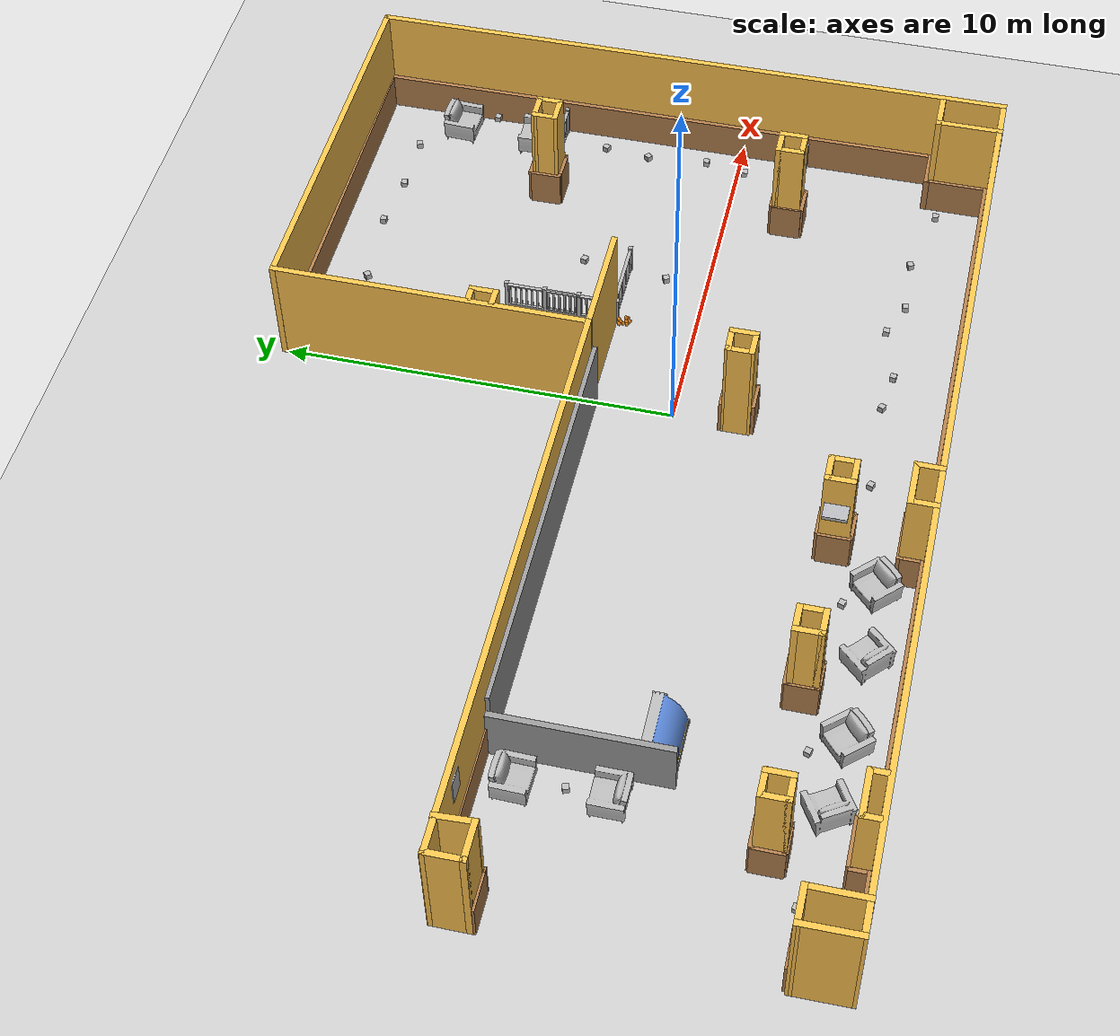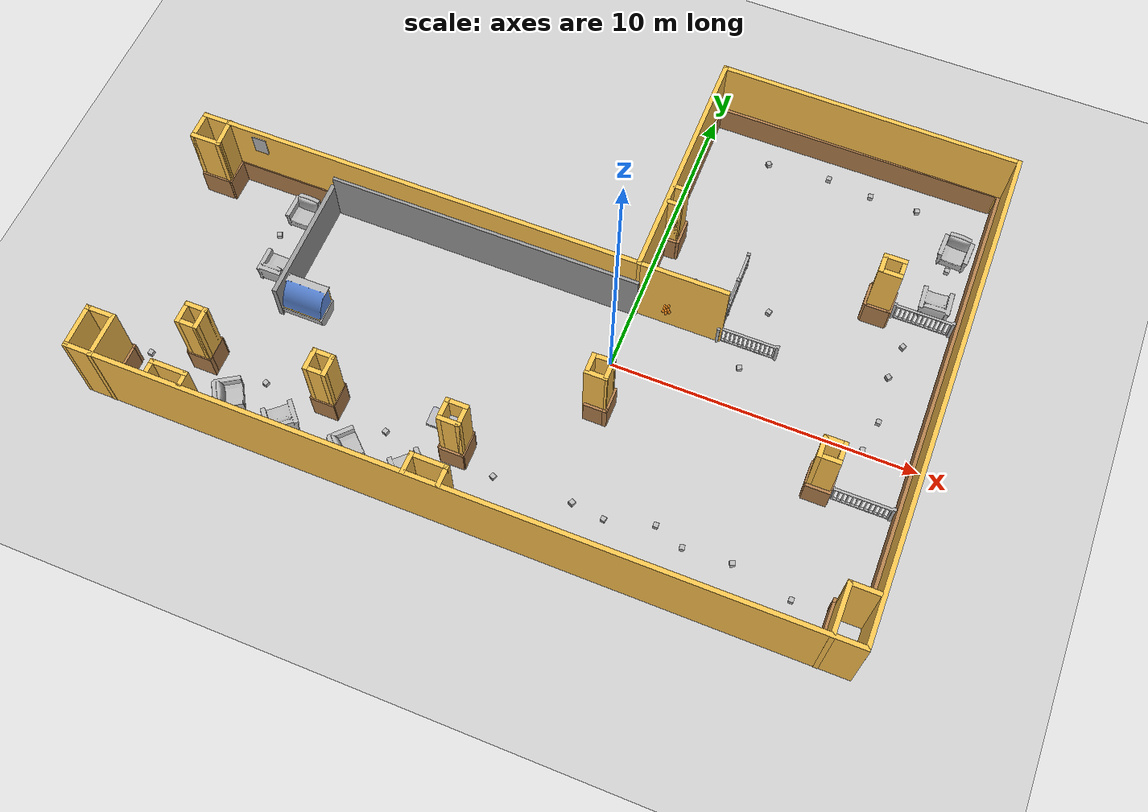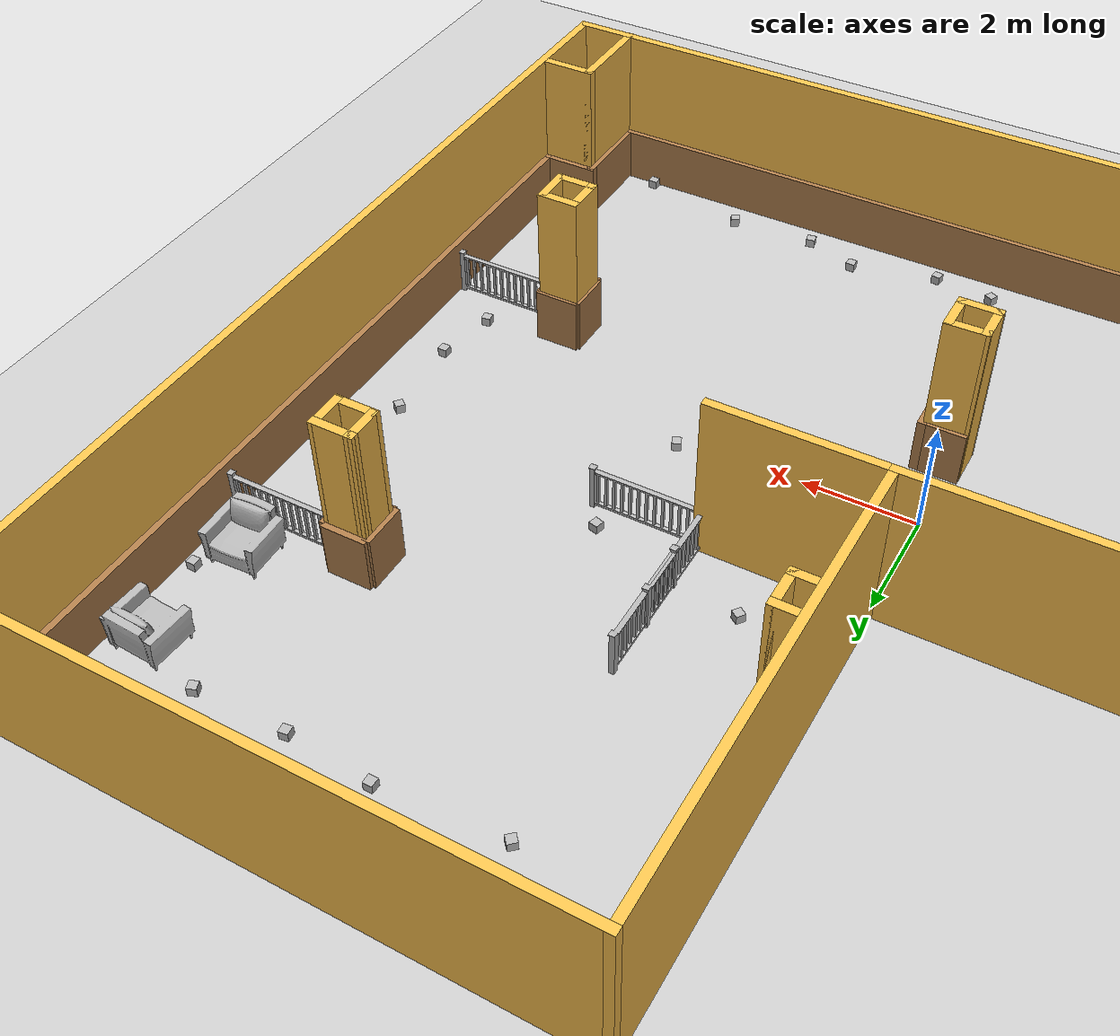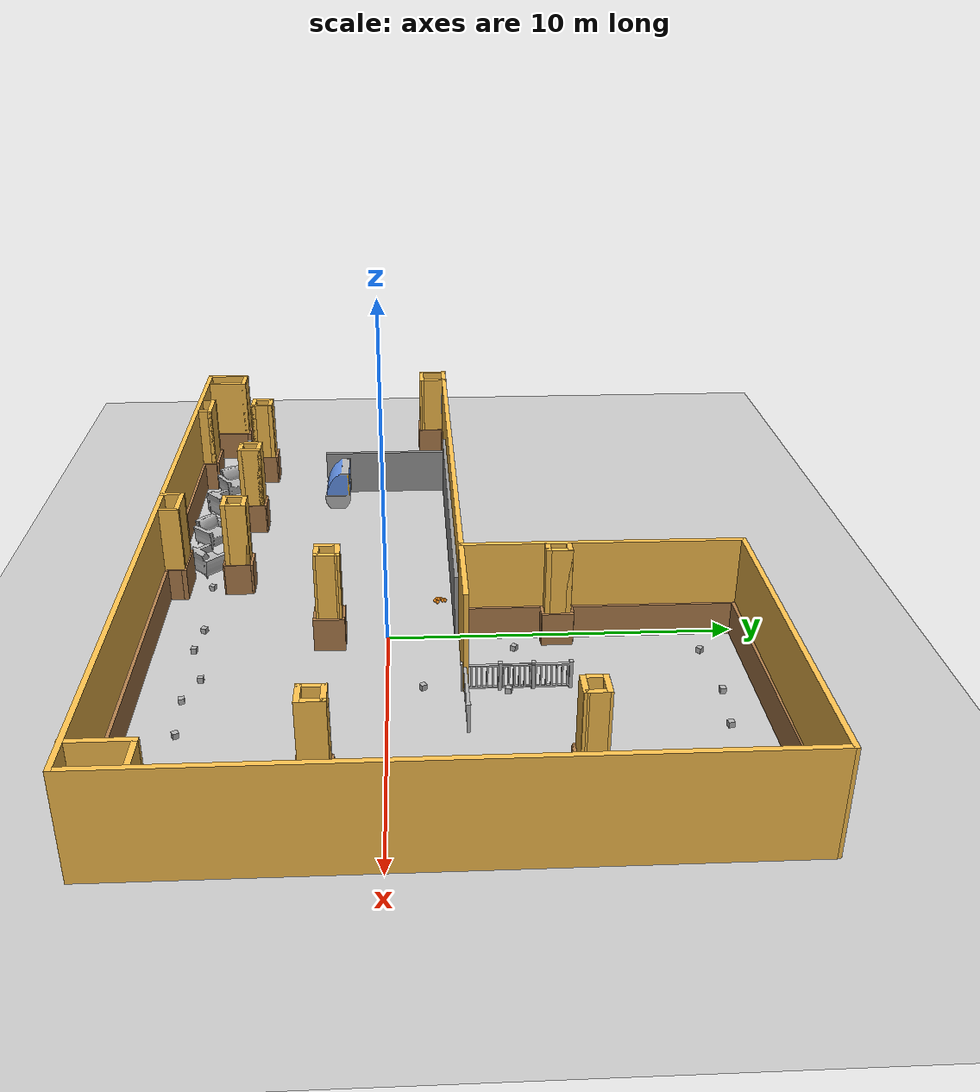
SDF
<sdf version="1.4">
 <world name="default">
  <light name="sun" type="directional">
   <cast_shadows>0</cast_shadows>
   <pose>0 0 10 0 -0 0</pose>
   <diffuse>0.8 0.8 0.8 1</diffuse>
   <specular>0.1 0.1 0.1 1</specular>
   <attenuation>
    <range>1000</range>
    <constant>0.9</constant>
    <linear>0.01</linear>
    <quadratic>0.001</quadratic>
   </attenuation>
   <direction>-0.5 0.5 -1</direction>
  </light>
  <model name="ground_plane">
   <static>1</static>
   <link name="link">
    <collision name="collision">
     <geometry><plane><normal>0 0 1</normal><size>100 100</size></plane></geometry>
     <surface><friction><ode><mu>100</mu><mu2>50</mu2></ode></friction></surface>
    </collision>
    <visual name="visual">
     <cast_shadows>0</cast_shadows>
     <geometry><plane><normal>0 0 1</normal><size>100 100</size></plane></geometry>
     <material>
      <script><uri>file://media/materials/scripts/gazebo.material</uri><name>Gazebo/Grey</name></script>
     </material>
    </visual>
   </link>
  </model>
  <physics name="default_physics" default="0" type="ode">
   <max_step_size>0.001</max_step_size>
   <real_time_factor>1</real_time_factor>
   <real_time_update_rate>1000</real_time_update_rate>
  </physics>
  <scene><ambient>0.4 0.4 0.4 1</ambient><background>0.7 0.7 0.7 1</background><shadows>0</shadows></scene>
  <spherical_coordinates>
   <surface_model>EARTH_WGS84</surface_model>
   <latitude_deg>0</latitude_deg>
   <longitude_deg>0</longitude_deg>
   <elevation>0</elevation>
   <heading_deg>0</heading_deg>
  </spherical_coordinates>
  <model name="costa-gv">
   <pose>-2.49048 1.64389 0 0 -0 0</pose>
   <link name="Wall_10">
    <collision name="Wall_10_Collision">
     <geometry><box><size>15 0.15 3</size></box></geometry>
     <pose>0 0 1.5 0 -0 0</pose>
    </collision>
    <visual name="Wall_10_Visual">
     <pose>0 0 1.5 0 -0 0</pose>
     <geometry><box><size>15 0.15 3</size></box></geometry>
     <material>
      <script><uri>file://media/materials/scripts/gazebo.material</uri><name>Gazebo/Grey</name></script>
      <ambient>1 0.764706 0.305882 1</ambient>
     </material>
    </visual>
    <pose>-4.93585 0.471568 0 0 -0 -3.14024</pose>
   </link>
   <link name="Wall_103">
    <collision name="Wall_103_Collision">
     <geometry><box><size>3.4811 0.15 1</size></box></geometry>
     <pose>0 0 0.5 0 -0 0</pose>
    </collision>
    <visual name="Wall_103_Visual">
     <pose>0 0 0.5 0 -0 0</pose>
     <geometry><box><size>3.4811 0.15 1</size></box></geometry>
     <material>
      <script><uri>file://media/materials/scripts/gazebo.material</uri><name>Gazebo/Wood</name></script>
      <ambient>1 1 1 1</ambient>
     </material>
    </visual>
    <pose>-9.76907 0.427453 0 0 -0 3.14152</pose>
   </link>
   <link name="Wall_108">
    <collision name="Wall_108_Collision">
     <geometry><box><size>1 0.15 1</size></box></geometry>
     <pose>0 0 0.5 0 -0 0</pose>
    </collision>
    <visual name="Wall_108_Visual">
     <pose>0 0 0.5 0 -0 0</pose>
     <geometry><box><size>1 0.15 1</size></box></geometry>
     <material>
      <script><uri>file://media/materials/scripts/gazebo.material</uri><name>Gazebo/Wood</name></script>
      <ambient>1 1 1 1</ambient>
     </material>
    </visual>
    <pose>-11.4344 -0.007502 0 0 -0 -1.5708</pose>
   </link>
   <link name="Wall_117">
    <collision name="Wall_117_Collision">
     <geometry><box><size>1 0.15 1</size></box></geometry>
     <pose>0 0 0.5 0 -0 0</pose>
    </collision>
    <visual name="Wall_117_Visual">
     <pose>0 0 0.5 0 -0 0</pose>
     <geometry><box><size>1 0.15 1</size></box></geometry>
     <material>
      <script><uri>file://media/materials/scripts/gazebo.material</uri><name>Gazebo/Wood</name></script>
      <ambient>1 1 1 1</ambient>
     </material>
    </visual>
    <pose>-11.9319 -0.439362 0 0 -0 0</pose>
   </link>
   <link name="Wall_122">
    <collision name="Wall_122_Collision">
     <geometry><box><size>1 0.15 1</size></box></geometry>
     <pose>0 0 0.5 0 -0 0</pose>
    </collision>
    <visual name="Wall_122_Visual">
     <pose>0 0 0.5 0 -0 0</pose>
     <geometry><box><size>1 0.15 1</size></box></geometry>
     <material>
      <script><uri>file://media/materials/scripts/gazebo.material</uri><name>Gazebo/Wood</name></script>
      <ambient>1 1 1 1</ambient>
     </material>
    </visual>
    <pose>-11.8018 -7.05636 0 0 -0 0</pose>
   </link>
   <link name="Wall_124">
    <collision name="Wall_124_Collision">
     <geometry><box><size>1.25 0.15 1</size></box></geometry>
     <pose>0 0 0.5 0 -0 0</pose>
    </collision>
    <visual name="Wall_124_Visual">
     <pose>0 0 0.5 0 -0 0</pose>
     <geometry><box><size>1.25 0.15 1</size></box></geometry>
     <material>
      <script><uri>file://media/materials/scripts/gazebo.material</uri><name>Gazebo/Wood</name></script>
      <ambient>1 1 1 1</ambient>
     </material>
    </visual>
    <pose>-11.3608 -7.72636 0 0 -0 -1.5708</pose>
   </link>
   <link name="Wall_126">
    <collision name="Wall_126_Collision">
     <geometry><box><size>1.75 0.15 1</size></box></geometry>
     <pose>0 0 0.5 0 -0 0</pose>
    </collision>
    <visual name="Wall_126_Visual">
     <pose>0 0 0.5 0 -0 0</pose>
     <geometry><box><size>1.75 0.15 1</size></box></geometry>
     <material>
      <script><uri>file://media/materials/scripts/gazebo.material</uri><name>Gazebo/Wood</name></script>
      <ambient>1 1 1 1</ambient>
     </material>
    </visual>
    <pose>-10.5508 -8.37536 0 0 -0 0</pose>
   </link>
   <link name="Wall_128">
    <collision name="Wall_128_Collision">
     <geometry><box><size>1.25 0.15 1</size></box></geometry>
     <pose>0 0 0.5 0 -0 0</pose>
    </collision>
    <visual name="Wall_128_Visual">
     <pose>0 0 0.5 0 -0 0</pose>
     <geometry><box><size>1.25 0.15 1</size></box></geometry>
     <material>
      <script><uri>file://media/materials/scripts/gazebo.material</uri><name>Gazebo/Wood</name></script>
      <ambient>1 1 1 1</ambient>
     </material>
    </visual>
    <pose>-9.08885 -7.91136 0 0 -0 0</pose>
   </link>
   <link name="Wall_130">
    <collision name="Wall_130_Collision">
     <geometry><box><size>0.5 0.15 1</size></box></geometry>
     <pose>0 0 0.5 0 -0 0</pose>
    </collision>
    <visual name="Wall_130_Visual">
     <pose>0 0 0.5 0 -0 0</pose>
     <geometry><box><size>0.5 0.15 1</size></box></geometry>
     <material>
      <script><uri>file://media/materials/scripts/gazebo.material</uri><name>Gazebo/Wood</name></script>
      <ambient>1 1 1 1</ambient>
     </material>
    </visual>
    <pose>-8.42085 -8.15736 0 0 -0 -1.5708</pose>
   </link>
   <link name="Wall_132">
    <collision name="Wall_132_Collision">
     <geometry><box><size>0.5 0.15 1</size></box></geometry>
     <pose>0 0 0.5 0 -0 0</pose>
    </collision>
    <visual name="Wall_132_Visual">
     <pose>0 0 0.5 0 -0 0</pose>
     <geometry><box><size>0.5 0.15 1</size></box></geometry>
     <material>
      <script><uri>file://media/materials/scripts/gazebo.material</uri><name>Gazebo/Wood</name></script>
      <ambient>1 1 1 1</ambient>
     </material>
    </visual>
    <pose>-9.72985 -8.13736 0 0 -0 -1.5708</pose>
   </link>
   <link name="Wall_134">
    <collision name="Wall_134_Collision">
     <geometry><box><size>7 0.15 1</size></box></geometry>
     <pose>0 0 0.5 0 -0 0</pose>
    </collision>
    <visual name="Wall_134_Visual">
     <pose>0 0 0.5 0 -0 0</pose>
     <geometry><box><size>7 0.15 1</size></box></geometry>
     <material>
      <script><uri>file://media/materials/scripts/gazebo.material</uri><name>Gazebo/Wood</name></script>
      <ambient>1 1 1 1</ambient>
     </material>
    </visual>
    <pose>-4.89485 -8.37536 0 0 -0 0</pose>
   </link>
   <link name="Wall_137">
    <collision name="Wall_137_Collision">
     <geometry><box><size>0.5 0.15 1</size></box></geometry>
     <pose>0 0 0.5 0 -0 0</pose>
    </collision>
    <visual name="Wall_137_Visual">
     <pose>0 0 0.5 0 -0 0</pose>
     <geometry><box><size>0.5 0.15 1</size></box></geometry>
     <material>
      <script><uri>file://media/materials/scripts/gazebo.material</uri><name>Gazebo/Wood</name></script>
      <ambient>1 1 1 1</ambient>
     </material>
    </visual>
    <pose>-1.42185 -8.07636 0 0 -0 -1.5708</pose>
   </link>
   <link name="Wall_141">
    <collision name="Wall_141_Collision">
     <geometry><box><size>0.8 0.15 1</size></box></geometry>
     <pose>0 0 0.5 0 -0 0</pose>
    </collision>
    <visual name="Wall_141_Visual">
     <pose>0 0 0.5 0 -0 0</pose>
     <geometry><box><size>0.8 0.15 1</size></box></geometry>
     <material>
      <script><uri>file://media/materials/scripts/gazebo.material</uri><name>Gazebo/Wood</name></script>
      <ambient>1 1 1 1</ambient>
     </material>
    </visual>
    <pose>-9.29371 -6.54229 0 0 -0 0</pose>
   </link>
   <link name="Wall_146">
    <collision name="Wall_146_Collision">
     <geometry><box><size>0.8 0.15 1</size></box></geometry>
     <pose>0 0 0.5 0 -0 0</pose>
    </collision>
    <visual name="Wall_146_Visual">
     <pose>0 0 0.5 0 -0 0</pose>
     <geometry><box><size>0.8 0.15 1</size></box></geometry>
     <material>
      <script><uri>file://media/materials/scripts/gazebo.material</uri><name>Gazebo/Wood</name></script>
      <ambient>1 1 1 1</ambient>
     </material>
    </visual>
    <pose>-9.30375 -5.81726 0 0 -0 0</pose>
   </link>
   <link name="Wall_148">
    <collision name="Wall_148_Collision">
     <geometry><box><size>0.8 0.15 1</size></box></geometry>
     <pose>0 0 0.5 0 -0 0</pose>
    </collision>
    <visual name="Wall_148_Visual">
     <pose>0 0 0.5 0 -0 0</pose>
     <geometry><box><size>0.8 0.15 1</size></box></geometry>
     <material>
      <script><uri>file://media/materials/scripts/gazebo.material</uri><name>Gazebo/Wood</name></script>
      <ambient>1 1 1 1</ambient>
     </material>
    </visual>
    <pose>-8.9742 -6.19261 0 0 -0 -1.5708</pose>
   </link>
   <link name="Wall_150">
    <collision name="Wall_150_Collision">
     <geometry><box><size>0.8 0.15 1</size></box></geometry>
     <pose>0 0 0.5 0 -0 0</pose>
    </collision>
    <visual name="Wall_150_Visual">
     <pose>0 0 0.5 0 -0 0</pose>
     <geometry><box><size>0.8 0.15 1</size></box></geometry>
     <material>
      <script><uri>file://media/materials/scripts/gazebo.material</uri><name>Gazebo/Wood</name></script>
      <ambient>1 1 1 1</ambient>
     </material>
    </visual>
    <pose>-9.66903 -6.18254 0 0 -0 -1.5708</pose>
   </link>
   <link name="Wall_152">
    <collision name="Wall_152_Collision">
     <geometry><box><size>0.8 0.15 1</size></box></geometry>
     <pose>0 0 0.5 0 -0 0</pose>
    </collision>
    <visual name="Wall_152_Visual">
     <pose>0 0 0.5 0 -0 0</pose>
     <geometry><box><size>0.8 0.15 1</size></box></geometry>
     <material>
      <script><uri>file://media/materials/scripts/gazebo.material</uri><name>Gazebo/Wood</name></script>
      <ambient>1 1 1 1</ambient>
     </material>
    </visual>
    <pose>-5.07028 -6.54841 0 0 -0 0</pose>
   </link>
   <link name="Wall_154">
    <collision name="Wall_154_Collision">
     <geometry><box><size>0.8 0.15 1</size></box></geometry>
     <pose>0 0 0.5 0 -0 0</pose>
    </collision>
    <visual name="Wall_154_Visual">
     <pose>0 0 0.5 0 -0 0</pose>
     <geometry><box><size>0.8 0.15 1</size></box></geometry>
     <material>
      <script><uri>file://media/materials/scripts/gazebo.material</uri><name>Gazebo/Wood</name></script>
      <ambient>1 1 1 1</ambient>
     </material>
    </visual>
    <pose>-5.07028 -5.82927 0 0 -0 0</pose>
   </link>
   <link name="Wall_156">
    <collision name="Wall_156_Collision">
     <geometry><box><size>0.8 0.15 1</size></box></geometry>
     <pose>0 0 0.5 0 -0 0</pose>
    </collision>
    <visual name="Wall_156_Visual">
     <pose>0 0 0.5 0 -0 0</pose>
     <geometry><box><size>0.8 0.15 1</size></box></geometry>
     <material>
      <script><uri>file://media/materials/scripts/gazebo.material</uri><name>Gazebo/Wood</name></script>
      <ambient>1 1 1 1</ambient>
     </material>
    </visual>
    <pose>-4.7294 -6.19422 0 0 -0 -1.5708</pose>
   </link>
   <link name="Wall_158">
    <collision name="Wall_158_Collision">
     <geometry><box><size>0.8 0.15 1</size></box></geometry>
     <pose>0 0 0.5 0 -0 0</pose>
    </collision>
    <visual name="Wall_158_Visual">
     <pose>0 0 0.5 0 -0 0</pose>
     <geometry><box><size>0.8 0.15 1</size></box></geometry>
     <material>
      <script><uri>file://media/materials/scripts/gazebo.material</uri><name>Gazebo/Wood</name></script>
      <ambient>1 1 1 1</ambient>
     </material>
    </visual>
    <pose>-5.42191 -6.19422 0 0 -0 -1.5708</pose>
   </link>
   <link name="Wall_160">
    <collision name="Wall_160_Collision">
     <geometry><box><size>1.4 0.15 1</size></box></geometry>
     <pose>0 0 0.5 0 -0 0</pose>
    </collision>
    <visual name="Wall_160_Visual">
     <pose>0 0 0.5 0 -0 0</pose>
     <geometry><box><size>1.4 0.15 1</size></box></geometry>
     <material>
      <script><uri>file://media/materials/scripts/gazebo.material</uri><name>Gazebo/Wood</name></script>
      <ambient>1 1 1 1</ambient>
     </material>
    </visual>
    <pose>-0.788355 -7.81357 0 0 -0 0</pose>
   </link>
   <link name="Wall_162">
    <collision name="Wall_162_Collision">
     <geometry><box><size>0.7 0.15 1</size></box></geometry>
     <pose>0 0 0.5 0 -0 0</pose>
    </collision>
    <visual name="Wall_162_Visual">
     <pose>0 0 0.5 0 -0 0</pose>
     <geometry><box><size>0.7 0.15 1</size></box></geometry>
     <material>
      <script><uri>file://media/materials/scripts/gazebo.material</uri><name>Gazebo/Wood</name></script>
      <ambient>1 1 1 1</ambient>
     </material>
    </visual>
    <pose>-0.174848 -8.16836 0 0 -0 -1.5708</pose>
   </link>
   <link name="Wall_167">
    <collision name="Wall_167_Collision">
     <geometry><box><size>0.8 0.15 1</size></box></geometry>
     <pose>0 0 0.5 0 -0 0</pose>
    </collision>
    <visual name="Wall_167_Visual">
     <pose>0 0 0.5 0 -0 0</pose>
     <geometry><box><size>0.8 0.15 1</size></box></geometry>
     <material>
      <script><uri>file://media/materials/scripts/gazebo.material</uri><name>Gazebo/Wood</name></script>
      <ambient>1 1 1 1</ambient>
     </material>
    </visual>
    <pose>-1.13366 -6.23417 0 0 -0 -1.5708</pose>
   </link>
   <link name="Wall_169">
    <collision name="Wall_169_Collision">
     <geometry><box><size>0.8 0.15 1</size></box></geometry>
     <pose>0 0 0.5 0 -0 0</pose>
    </collision>
    <visual name="Wall_169_Visual">
     <pose>0 0 0.5 0 -0 0</pose>
     <geometry><box><size>0.8 0.15 1</size></box></geometry>
     <material>
      <script><uri>file://media/materials/scripts/gazebo.material</uri><name>Gazebo/Wood</name></script>
      <ambient>1 1 1 1</ambient>
     </material>
    </visual>
    <pose>-0.414512 -6.23417 0 0 -0 -1.5708</pose>
   </link>
   <link name="Wall_171">
    <collision name="Wall_171_Collision">
     <geometry><box><size>0.8 0.15 1</size></box></geometry>
     <pose>0 0 0.5 0 -0 0</pose>
    </collision>
    <visual name="Wall_171_Visual">
     <pose>0 0 0.5 0 -0 0</pose>
     <geometry><box><size>0.8 0.15 1</size></box></geometry>
     <material>
      <script><uri>file://media/materials/scripts/gazebo.material</uri><name>Gazebo/Wood</name></script>
      <ambient>1 1 1 1</ambient>
     </material>
    </visual>
    <pose>-0.768707 -6.60168 0 0 -0 0</pose>
   </link>
   <link name="Wall_173">
    <collision name="Wall_173_Collision">
     <geometry><box><size>0.8 0.15 1</size></box></geometry>
     <pose>0 0 0.5 0 -0 0</pose>
    </collision>
    <visual name="Wall_173_Visual">
     <pose>0 0 0.5 0 -0 0</pose>
     <geometry><box><size>0.8 0.15 1</size></box></geometry>
     <material>
      <script><uri>file://media/materials/scripts/gazebo.material</uri><name>Gazebo/Wood</name></script>
      <ambient>1 1 1 1</ambient>
     </material>
    </visual>
    <pose>-0.75539 -5.84258 0 0 -0 0</pose>
   </link>
   <link name="Wall_175">
    <collision name="Wall_175_Collision">
     <geometry><box><size>11.5 0.15 1</size></box></geometry>
     <pose>0 0 0.5 0 -0 0</pose>
    </collision>
    <visual name="Wall_175_Visual">
     <pose>0 0 0.5 0 -0 0</pose>
     <geometry><box><size>11.5 0.15 1</size></box></geometry>
     <material>
      <script><uri>file://media/materials/scripts/gazebo.material</uri><name>Gazebo/Wood</name></script>
      <ambient>1 1 1 1</ambient>
     </material>
    </visual>
    <pose>5.58313 -8.36284 0 0 -0 0</pose>
   </link>
   <link name="Wall_177">
    <collision name="Wall_177_Collision">
     <geometry><box><size>1.6 0.15 1</size></box></geometry>
     <pose>0 0 0.5 0 -0 0</pose>
    </collision>
    <visual name="Wall_177_Visual">
     <pose>0 0 0.5 0 -0 0</pose>
     <geometry><box><size>1.6 0.15 1</size></box></geometry>
     <material>
      <script><uri>file://media/materials/scripts/gazebo.material</uri><name>Gazebo/Wood</name></script>
      <ambient>1 1 1 1</ambient>
     </material>
    </visual>
    <pose>11.2848 -7.54313 0 0 -0 -1.5708</pose>
   </link>
   <link name="Wall_179">
    <collision name="Wall_179_Collision">
     <geometry><box><size>1.15 0.15 1</size></box></geometry>
     <pose>0 0 0.5 0 -0 0</pose>
    </collision>
    <visual name="Wall_179_Visual">
     <pose>0 0 0.5 0 -0 0</pose>
     <geometry><box><size>1.15 0.15 1</size></box></geometry>
     <material>
      <script><uri>file://media/materials/scripts/gazebo.material</uri><name>Gazebo/Wood</name></script>
      <ambient>1 1 1 1</ambient>
     </material>
    </visual>
    <pose>11.7805 -6.77121 0 0 -0 3.14159</pose>
   </link>
   <link name="Wall_181">
    <collision name="Wall_181_Collision">
     <geometry><box><size>0.75 0.15 1</size></box></geometry>
     <pose>0 0 0.5 0 -0 0</pose>
    </collision>
    <visual name="Wall_181_Visual">
     <pose>0 0 0.5 0 -0 0</pose>
     <geometry><box><size>0.75 0.15 1</size></box></geometry>
     <material>
      <script><uri>file://media/materials/scripts/gazebo.material</uri><name>Gazebo/Wood</name></script>
      <ambient>1 1 1 1</ambient>
     </material>
    </visual>
    <pose>2.70847 -3.64523 0 0 -0 0</pose>
   </link>
   <link name="Wall_183">
    <collision name="Wall_183_Collision">
     <geometry><box><size>0.9 0.15 1</size></box></geometry>
     <pose>0 0 0.5 0 -0 0</pose>
    </collision>
    <visual name="Wall_183_Visual">
     <pose>0 0 0.5 0 -0 0</pose>
     <geometry><box><size>0.9 0.15 1</size></box></geometry>
     <material>
      <script><uri>file://media/materials/scripts/gazebo.material</uri><name>Gazebo/Wood</name></script>
      <ambient>1 1 1 1</ambient>
     </material>
    </visual>
    <pose>3.03515 -3.27436 0 0 -0 -1.5708</pose>
   </link>
   <link name="Wall_185">
    <collision name="Wall_185_Collision">
     <geometry><box><size>0.75 0.15 1</size></box></geometry>
     <pose>0 0 0.5 0 -0 0</pose>
    </collision>
    <visual name="Wall_185_Visual">
     <pose>0 0 0.5 0 -0 0</pose>
     <geometry><box><size>0.75 0.15 1</size></box></geometry>
     <material>
      <script><uri>file://media/materials/scripts/gazebo.material</uri><name>Gazebo/Wood</name></script>
      <ambient>1 1 1 1</ambient>
     </material>
    </visual>
    <pose>2.65506 -2.89971 0 0 -0 0</pose>
   </link>
   <link name="Wall_187">
    <collision name="Wall_187_Collision">
     <geometry><box><size>0.8 0.15 1</size></box></geometry>
     <pose>0 0 0.5 0 -0 0</pose>
    </collision>
    <visual name="Wall_187_Visual">
     <pose>0 0 0.5 0 -0 0</pose>
     <geometry><box><size>0.8 0.15 1</size></box></geometry>
     <material>
      <script><uri>file://media/materials/scripts/gazebo.material</uri><name>Gazebo/Wood</name></script>
      <ambient>1 1 1 1</ambient>
     </material>
    </visual>
    <pose>10.133 -3.27767 0 0 -0 -1.5708</pose>
   </link>
   <link name="Wall_189">
    <collision name="Wall_189_Collision">
     <geometry><box><size>0.8 0.15 1</size></box></geometry>
     <pose>0 0 0.5 0 -0 0</pose>
    </collision>
    <visual name="Wall_189_Visual">
     <pose>0 0 0.5 0 -0 0</pose>
     <geometry><box><size>0.8 0.15 1</size></box></geometry>
     <material>
      <script><uri>file://media/materials/scripts/gazebo.material</uri><name>Gazebo/Wood</name></script>
      <ambient>1 1 1 1</ambient>
     </material>
    </visual>
    <pose>9.42716 -3.27767 0 0 -0 -1.5708</pose>
   </link>
   <link name="Wall_191">
    <collision name="Wall_191_Collision">
     <geometry><box><size>0.8 0.15 1</size></box></geometry>
     <pose>0 0 0.5 0 -0 0</pose>
    </collision>
    <visual name="Wall_191_Visual">
     <pose>0 0 0.5 0 -0 0</pose>
     <geometry><box><size>0.8 0.15 1</size></box></geometry>
     <material>
      <script><uri>file://media/materials/scripts/gazebo.material</uri><name>Gazebo/Wood</name></script>
      <ambient>1 1 1 1</ambient>
     </material>
    </visual>
    <pose>9.79211 -2.8994 0 0 -0 0</pose>
   </link>
   <link name="Wall_193">
    <collision name="Wall_193_Collision">
     <geometry><box><size>0.8 0.15 1</size></box></geometry>
     <pose>0 0 0.5 0 -0 0</pose>
    </collision>
    <visual name="Wall_193_Visual">
     <pose>0 0 0.5 0 -0 0</pose>
     <geometry><box><size>0.8 0.15 1</size></box></geometry>
     <material>
      <script><uri>file://media/materials/scripts/gazebo.material</uri><name>Gazebo/Wood</name></script>
      <ambient>1 1 1 1</ambient>
     </material>
    </visual>
    <pose>9.79211 -3.6585 0 0 -0 0</pose>
   </link>
   <link name="Wall_195">
    <collision name="Wall_195_Collision">
     <geometry><box><size>2.5 0.15 1</size></box></geometry>
     <pose>0 0 0.5 0 -0 0</pose>
    </collision>
    <visual name="Wall_195_Visual">
     <pose>0 0 0.5 0 -0 0</pose>
     <geometry><box><size>2.5 0.15 1</size></box></geometry>
     <material>
      <script><uri>file://media/materials/scripts/gazebo.material</uri><name>Gazebo/Wood</name></script>
      <ambient>1 1 1 1</ambient>
     </material>
    </visual>
    <pose>2.58315 1.69081 0 0 -0 -1.5708</pose>
   </link>
   <link name="Wall_199">
    <collision name="Wall_199_Collision">
     <geometry><box><size>0.9 0.15 1</size></box></geometry>
     <pose>0 0 0.5 0 -0 0</pose>
    </collision>
    <visual name="Wall_199_Visual">
     <pose>0 0 0.5 0 -0 0</pose>
     <geometry><box><size>0.9 0.15 1</size></box></geometry>
     <material>
      <script><uri>file://media/materials/scripts/gazebo.material</uri><name>Gazebo/Wood</name></script>
      <ambient>1 1 1 1</ambient>
     </material>
    </visual>
    <pose>3.02615 3.21247 0 0 -0 -1.5708</pose>
   </link>
   <link name="Wall_20">
    <collision name="Wall_20_Collision">
     <geometry><box><size>0.75 0.15 3</size></box></geometry>
     <pose>0 0 1.5 0 -0 0</pose>
    </collision>
    <visual name="Wall_20_Visual">
     <pose>0 0 1.5 0 -0 0</pose>
     <geometry><box><size>0.75 0.15 3</size></box></geometry>
     <material>
      <script><uri>file://media/materials/scripts/gazebo.material</uri><name>Gazebo/Grey</name></script>
      <ambient>1 0.764706 0.305882 1</ambient>
     </material>
    </visual>
    <pose>-9.28985 -5.90136 0 0 -0 0</pose>
   </link>
   <link name="Wall_201">
    <collision name="Wall_201_Collision">
     <geometry><box><size>0.5 0.15 1</size></box></geometry>
     <pose>0 0 0.5 0 -0 0</pose>
    </collision>
    <visual name="Wall_201_Visual">
     <pose>0 0 0.5 0 -0 0</pose>
     <geometry><box><size>0.5 0.15 1</size></box></geometry>
     <material>
      <script><uri>file://media/materials/scripts/gazebo.material</uri><name>Gazebo/Wood</name></script>
      <ambient>1 1 1 1</ambient>
     </material>
    </visual>
    <pose>2.75815 2.81964 0 0 -0 3.14159</pose>
   </link>
   <link name="Wall_203">
    <collision name="Wall_203_Collision">
     <geometry><box><size>0.5 0.15 1</size></box></geometry>
     <pose>0 0 0.5 0 -0 0</pose>
    </collision>
    <visual name="Wall_203_Visual">
     <pose>0 0 0.5 0 -0 0</pose>
     <geometry><box><size>0.5 0.15 1</size></box></geometry>
     <material>
      <script><uri>file://media/materials/scripts/gazebo.material</uri><name>Gazebo/Wood</name></script>
      <ambient>1 1 1 1</ambient>
     </material>
    </visual>
    <pose>2.73412 3.61144 0 0 -0 3.14159</pose>
   </link>
   <link name="Wall_205">
    <collision name="Wall_205_Collision">
     <geometry><box><size>4.75 0.15 1</size></box></geometry>
     <pose>0 0 0.5 0 -0 0</pose>
    </collision>
    <visual name="Wall_205_Visual">
     <pose>0 0 0.5 0 -0 0</pose>
     <geometry><box><size>4.75 0.15 1</size></box></geometry>
     <material>
      <script><uri>file://media/materials/scripts/gazebo.material</uri><name>Gazebo/Wood</name></script>
      <ambient>1 1 1 1</ambient>
     </material>
    </visual>
    <pose>2.60715 6.03935 0 0 -0 -1.5708</pose>
   </link>
   <link name="Wall_207">
    <collision name="Wall_207_Collision">
     <geometry><box><size>0.8 0.15 1</size></box></geometry>
     <pose>0 0 0.5 0 -0 0</pose>
    </collision>
    <visual name="Wall_207_Visual">
     <pose>0 0 0.5 0 -0 0</pose>
     <geometry><box><size>0.8 0.15 1</size></box></geometry>
     <material>
      <script><uri>file://media/materials/scripts/gazebo.material</uri><name>Gazebo/Wood</name></script>
      <ambient>1 1 1 1</ambient>
     </material>
    </visual>
    <pose>9.6862 3.63471 0 0 -0 0</pose>
   </link>
   <link name="Wall_209">
    <collision name="Wall_209_Collision">
     <geometry><box><size>0.8 0.15 1</size></box></geometry>
     <pose>0 0 0.5 0 -0 0</pose>
    </collision>
    <visual name="Wall_209_Visual">
     <pose>0 0 0.5 0 -0 0</pose>
     <geometry><box><size>0.8 0.15 1</size></box></geometry>
     <material>
      <script><uri>file://media/materials/scripts/gazebo.material</uri><name>Gazebo/Wood</name></script>
      <ambient>1 1 1 1</ambient>
     </material>
    </visual>
    <pose>9.70978 2.88914 0 0 -0 0</pose>
   </link>
   <link name="Wall_21">
    <collision name="Wall_21_Collision">
     <geometry><box><size>0.75 0.15 3</size></box></geometry>
     <pose>0 0 1.5 0 -0 0</pose>
    </collision>
    <visual name="Wall_21_Visual">
     <pose>0 0 1.5 0 -0 0</pose>
     <geometry><box><size>0.75 0.15 3</size></box></geometry>
     <material>
      <script><uri>file://media/materials/scripts/gazebo.material</uri><name>Gazebo/Grey</name></script>
      <ambient>1 0.764706 0.305882 1</ambient>
     </material>
    </visual>
    <pose>-8.98985 -6.20136 0 0 -0 -1.5708</pose>
   </link>
   <link name="Wall_211">
    <collision name="Wall_211_Collision">
     <geometry><box><size>0.8 0.15 1</size></box></geometry>
     <pose>0 0 0.5 0 -0 0</pose>
    </collision>
    <visual name="Wall_211_Visual">
     <pose>0 0 0.5 0 -0 0</pose>
     <geometry><box><size>0.8 0.15 1</size></box></geometry>
     <material>
      <script><uri>file://media/materials/scripts/gazebo.material</uri><name>Gazebo/Wood</name></script>
      <ambient>1 1 1 1</ambient>
     </material>
    </visual>
    <pose>10.0836 3.23963 0 0 -0 -1.5708</pose>
   </link>
   <link name="Wall_213">
    <collision name="Wall_213_Collision">
     <geometry><box><size>0.8 0.15 1</size></box></geometry>
     <pose>0 0 0.5 0 -0 0</pose>
    </collision>
    <visual name="Wall_213_Visual">
     <pose>0 0 0.5 0 -0 0</pose>
     <geometry><box><size>0.8 0.15 1</size></box></geometry>
     <material>
      <script><uri>file://media/materials/scripts/gazebo.material</uri><name>Gazebo/Wood</name></script>
      <ambient>1 1 1 1</ambient>
     </material>
    </visual>
    <pose>9.31515 3.23964 0 0 -0 -1.5708</pose>
   </link>
   <link name="Wall_215">
    <collision name="Wall_215_Collision">
     <geometry><box><size>9.5 0.15 1</size></box></geometry>
     <pose>0 0 0.5 0 -0 0</pose>
    </collision>
    <visual name="Wall_215_Visual">
     <pose>0 0 0.5 0 -0 0</pose>
     <geometry><box><size>9.5 0.15 1</size></box></geometry>
     <material>
      <script><uri>file://media/materials/scripts/gazebo.material</uri><name>Gazebo/Wood</name></script>
      <ambient>1 1 1 1</ambient>
     </material>
    </visual>
    <pose>7.37515 8.36264 0 0 -0 0</pose>
   </link>
   <link name="Wall_217">
    <collision name="Wall_217_Collision">
     <geometry><box><size>15.25 0.15 1</size></box></geometry>
     <pose>0 0 0.5 0 -0 0</pose>
    </collision>
    <visual name="Wall_217_Visual">
     <pose>0 0 0.5 0 -0 0</pose>
     <geometry><box><size>15.25 0.15 1</size></box></geometry>
     <material>
      <script><uri>file://media/materials/scripts/gazebo.material</uri><name>Gazebo/Wood</name></script>
      <ambient>1 1 1 1</ambient>
     </material>
    </visual>
    <pose>12.2443 0.762065 0 0 -0 -1.5708</pose>
   </link>
   <link name="Wall_219">
    <collision name="Wall_219_Collision">
     <geometry><box><size>10.5 0.15 2</size></box></geometry>
     <pose>0 0 1 0 -0 0</pose>
    </collision>
    <visual name="Wall_219_Visual">
     <pose>0 0 1 0 -0 0</pose>
     <geometry><box><size>10.5 0.15 2</size></box></geometry>
     <material>
      <script><uri>file://media/materials/scripts/gazebo.material</uri><name>Gazebo/Grey</name></script>
      <ambient>1 1 1 1</ambient>
     </material>
    </visual>
    <pose>-2.66326 0.365931 0 0 -0 3.14159</pose>
   </link>
   <link name="Wall_22">
    <collision name="Wall_22_Collision">
     <geometry><box><size>0.75 0.15 3</size></box></geometry>
     <pose>0 0 1.5 0 -0 0</pose>
    </collision>
    <visual name="Wall_22_Visual">
     <pose>0 0 1.5 0 -0 0</pose>
     <geometry><box><size>0.75 0.15 3</size></box></geometry>
     <material>
      <script><uri>file://media/materials/scripts/gazebo.material</uri><name>Gazebo/Grey</name></script>
      <ambient>1 0.764706 0.305882 1</ambient>
     </material>
    </visual>
    <pose>-9.28985 -6.50136 0 0 -0 3.14159</pose>
   </link>
   <link name="Wall_23">
    <collision name="Wall_23_Collision">
     <geometry><box><size>0.75 0.15 3</size></box></geometry>
     <pose>0 0 1.5 0 -0 0</pose>
    </collision>
    <visual name="Wall_23_Visual">
     <pose>0 0 1.5 0 -0 0</pose>
     <geometry><box><size>0.75 0.15 3</size></box></geometry>
     <material>
      <script><uri>file://media/materials/scripts/gazebo.material</uri><name>Gazebo/Grey</name></script>
      <ambient>1 0.764706 0.305882 1</ambient>
     </material>
    </visual>
    <pose>-9.58985 -6.20136 0 0 -0 1.5708</pose>
   </link>
   <link name="Wall_25">
    <collision name="Wall_25_Collision">
     <geometry><box><size>0.75 0.15 3</size></box></geometry>
     <pose>0 0 1.5 0 -0 0</pose>
    </collision>
    <visual name="Wall_25_Visual">
     <pose>0 0 1.5 0 -0 0</pose>
     <geometry><box><size>0.75 0.15 3</size></box></geometry>
     <material>
      <script><uri>file://media/materials/scripts/gazebo.material</uri><name>Gazebo/Grey</name></script>
      <ambient>1 0.764706 0.305882 1</ambient>
     </material>
    </visual>
    <pose>-5.05985 -5.90136 0 0 -0 0</pose>
   </link>
   <link name="Wall_26">
    <collision name="Wall_26_Collision">
     <geometry><box><size>0.75 0.15 3</size></box></geometry>
     <pose>0 0 1.5 0 -0 0</pose>
    </collision>
    <visual name="Wall_26_Visual">
     <pose>0 0 1.5 0 -0 0</pose>
     <geometry><box><size>0.75 0.15 3</size></box></geometry>
     <material>
      <script><uri>file://media/materials/scripts/gazebo.material</uri><name>Gazebo/Grey</name></script>
      <ambient>1 0.764706 0.305882 1</ambient>
     </material>
    </visual>
    <pose>-4.75985 -6.20136 0 0 -0 -1.5708</pose>
   </link>
   <link name="Wall_29">
    <collision name="Wall_29_Collision">
     <geometry><box><size>0.75 0.15 3</size></box></geometry>
     <pose>0 0 1.5 0 -0 0</pose>
    </collision>
    <visual name="Wall_29_Visual">
     <pose>0 0 1.5 0 -0 0</pose>
     <geometry><box><size>0.75 0.15 3</size></box></geometry>
     <material>
      <script><uri>file://media/materials/scripts/gazebo.material</uri><name>Gazebo/Grey</name></script>
      <ambient>1 0.764706 0.305882 1</ambient>
     </material>
    </visual>
    <pose>-5.35985 -6.20136 0 0 -0 -1.5708</pose>
   </link>
   <link name="Wall_30">
    <collision name="Wall_30_Collision">
     <geometry><box><size>0.75 0.15 3</size></box></geometry>
     <pose>0 0 1.5 0 -0 0</pose>
    </collision>
    <visual name="Wall_30_Visual">
     <pose>0 0 1.5 0 -0 0</pose>
     <geometry><box><size>0.75 0.15 3</size></box></geometry>
     <material>
      <script><uri>file://media/materials/scripts/gazebo.material</uri><name>Gazebo/Grey</name></script>
      <ambient>1 0.764706 0.305882 1</ambient>
     </material>
    </visual>
    <pose>-5.05985 -6.50136 0 0 -0 0</pose>
   </link>
   <link name="Wall_32">
    <collision name="Wall_32_Collision">
     <geometry><box><size>0.75 0.15 3</size></box></geometry>
     <pose>0 0 1.5 0 -0 0</pose>
    </collision>
    <visual name="Wall_32_Visual">
     <pose>0 0 1.5 0 -0 0</pose>
     <geometry><box><size>0.75 0.15 3</size></box></geometry>
     <material>
      <script><uri>file://media/materials/scripts/gazebo.material</uri><name>Gazebo/Grey</name></script>
      <ambient>1 0.764706 0.305882 1</ambient>
     </material>
    </visual>
    <pose>-0.759848 -5.92136 0 0 -0 0</pose>
   </link>
   <link name="Wall_33">
    <collision name="Wall_33_Collision">
     <geometry><box><size>0.75 0.15 3</size></box></geometry>
     <pose>0 0 1.5 0 -0 0</pose>
    </collision>
    <visual name="Wall_33_Visual">
     <pose>0 0 1.5 0 -0 0</pose>
     <geometry><box><size>0.75 0.15 3</size></box></geometry>
     <material>
      <script><uri>file://media/materials/scripts/gazebo.material</uri><name>Gazebo/Grey</name></script>
      <ambient>1 0.764706 0.305882 1</ambient>
     </material>
    </visual>
    <pose>-0.459848 -6.22136 0 0 -0 -1.5708</pose>
   </link>
   <link name="Wall_34">
    <collision name="Wall_34_Collision">
     <geometry><box><size>0.75 0.15 3</size></box></geometry>
     <pose>0 0 1.5 0 -0 0</pose>
    </collision>
    <visual name="Wall_34_Visual">
     <pose>0 0 1.5 0 -0 0</pose>
     <geometry><box><size>0.75 0.15 3</size></box></geometry>
     <material>
      <script><uri>file://media/materials/scripts/gazebo.material</uri><name>Gazebo/Grey</name></script>
      <ambient>1 0.764706 0.305882 1</ambient>
     </material>
    </visual>
    <pose>-0.759848 -6.52136 0 0 -0 3.14159</pose>
   </link>
   <link name="Wall_35">
    <collision name="Wall_35_Collision">
     <geometry><box><size>0.75 0.15 3</size></box></geometry>
     <pose>0 0 1.5 0 -0 0</pose>
    </collision>
    <visual name="Wall_35_Visual">
     <pose>0 0 1.5 0 -0 0</pose>
     <geometry><box><size>0.75 0.15 3</size></box></geometry>
     <material>
      <script><uri>file://media/materials/scripts/gazebo.material</uri><name>Gazebo/Grey</name></script>
      <ambient>1 0.764706 0.305882 1</ambient>
     </material>
    </visual>
    <pose>-1.05985 -6.22136 0 0 -0 1.5708</pose>
   </link>
   <link name="Wall_37">
    <collision name="Wall_37_Collision">
     <geometry><box><size>0.751 0.15 3</size></box></geometry>
     <pose>0 0 1.5 0 -0 0</pose>
    </collision>
    <visual name="Wall_37_Visual">
     <pose>0 0 1.5 0 -0 0</pose>
     <geometry><box><size>0.751 0.15 3</size></box></geometry>
     <material>
      <script><uri>file://media/materials/scripts/gazebo.material</uri><name>Gazebo/Grey</name></script>
      <ambient>1 0.764706 0.305882 1</ambient>
     </material>
    </visual>
    <pose>2.6549 -2.96586 0 0 -0 0.028256</pose>
   </link>
   <link name="Wall_38">
    <collision name="Wall_38_Collision">
     <geometry><box><size>0.73251 0.15 3</size></box></geometry>
     <pose>0 0 1.5 0 -0 0</pose>
    </collision>
    <visual name="Wall_38_Visual">
     <pose>0 0 1.5 0 -0 0</pose>
     <geometry><box><size>0.73251 0.15 3</size></box></geometry>
     <material>
      <script><uri>file://media/materials/scripts/gazebo.material</uri><name>Gazebo/Grey</name></script>
      <ambient>1 0.764706 0.305882 1</ambient>
     </material>
    </visual>
    <pose>2.9554 -3.26611 0 0 -0 -1.57164</pose>
   </link>
   <link name="Wall_39">
    <collision name="Wall_39_Collision">
     <geometry><box><size>0.75 0.15 3</size></box></geometry>
     <pose>0 0 1.5 0 -0 0</pose>
    </collision>
    <visual name="Wall_39_Visual">
     <pose>0 0 1.5 0 -0 0</pose>
     <geometry><box><size>0.75 0.15 3</size></box></geometry>
     <material>
      <script><uri>file://media/materials/scripts/gazebo.material</uri><name>Gazebo/Grey</name></script>
      <ambient>1 0.764706 0.305882 1</ambient>
     </material>
    </visual>
    <pose>2.65515 -3.55736 0 0 -0 3.14159</pose>
   </link>
   <link name="Wall_40">
    <collision name="Wall_40_Collision">
     <geometry><box><size>0.73251 0.15 3</size></box></geometry>
     <pose>0 0 1.5 0 -0 0</pose>
    </collision>
    <visual name="Wall_40_Visual">
     <pose>0 0 1.5 0 -0 0</pose>
     <geometry><box><size>0.73251 0.15 3</size></box></geometry>
     <material>
      <script><uri>file://media/materials/scripts/gazebo.material</uri><name>Gazebo/Grey</name></script>
      <ambient>1 0.764706 0.305882 1</ambient>
     </material>
    </visual>
    <pose>2.35465 -3.26586 0 0 -0 1.57251</pose>
   </link>
   <link name="Wall_42">
    <collision name="Wall_42_Collision">
     <geometry><box><size>0.75 0.15 3</size></box></geometry>
     <pose>0 0 1.5 0 -0 0</pose>
    </collision>
    <visual name="Wall_42_Visual">
     <pose>0 0 1.5 0 -0 0</pose>
     <geometry><box><size>0.75 0.15 3</size></box></geometry>
     <material>
      <script><uri>file://media/materials/scripts/gazebo.material</uri><name>Gazebo/Grey</name></script>
      <ambient>1 0.764706 0.305882 1</ambient>
     </material>
    </visual>
    <pose>9.77815 -2.95836 0 0 -0 0</pose>
   </link>
   <link name="Wall_43">
    <collision name="Wall_43_Collision">
     <geometry><box><size>0.75 0.15 3</size></box></geometry>
     <pose>0 0 1.5 0 -0 0</pose>
    </collision>
    <visual name="Wall_43_Visual">
     <pose>0 0 1.5 0 -0 0</pose>
     <geometry><box><size>0.75 0.15 3</size></box></geometry>
     <material>
      <script><uri>file://media/materials/scripts/gazebo.material</uri><name>Gazebo/Grey</name></script>
      <ambient>1 0.764706 0.305882 1</ambient>
     </material>
    </visual>
    <pose>10.0782 -3.25836 0 0 -0 -1.5708</pose>
   </link>
   <link name="Wall_44">
    <collision name="Wall_44_Collision">
     <geometry><box><size>0.749866 0.15 3</size></box></geometry>
     <pose>0 0 1.5 0 -0 0</pose>
    </collision>
    <visual name="Wall_44_Visual">
     <pose>0 0 1.5 0 -0 0</pose>
     <geometry><box><size>0.749866 0.15 3</size></box></geometry>
     <material>
      <script><uri>file://media/materials/scripts/gazebo.material</uri><name>Gazebo/Grey</name></script>
      <ambient>1 0.764706 0.305882 1</ambient>
     </material>
    </visual>
    <pose>9.77815 -3.55836 0 0 -0 3.14159</pose>
   </link>
   <link name="Wall_45">
    <collision name="Wall_45_Collision">
     <geometry><box><size>0.75 0.15 3</size></box></geometry>
     <pose>0 0 1.5 0 -0 0</pose>
    </collision>
    <visual name="Wall_45_Visual">
     <pose>0 0 1.5 0 -0 0</pose>
     <geometry><box><size>0.75 0.15 3</size></box></geometry>
     <material>
      <script><uri>file://media/materials/scripts/gazebo.material</uri><name>Gazebo/Grey</name></script>
      <ambient>1 0.764706 0.305882 1</ambient>
     </material>
    </visual>
    <pose>9.47815 -3.25836 0 0 -0 1.5708</pose>
   </link>
   <link name="Wall_47">
    <collision name="Wall_47_Collision">
     <geometry><box><size>0.5 0.15 3</size></box></geometry>
     <pose>0 0 1.5 0 -0 0</pose>
    </collision>
    <visual name="Wall_47_Visual">
     <pose>0 0 1.5 0 -0 0</pose>
     <geometry><box><size>0.5 0.15 3</size></box></geometry>
     <material>
      <script><uri>file://media/materials/scripts/gazebo.material</uri><name>Gazebo/Grey</name></script>
      <ambient>1 0.764706 0.305882 1</ambient>
     </material>
    </visual>
    <pose>2.77015 3.51064 0 0 -0 0</pose>
   </link>
   <link name="Wall_48">
    <collision name="Wall_48_Collision">
     <geometry><box><size>0.75 0.15 3</size></box></geometry>
     <pose>0 0 1.5 0 -0 0</pose>
    </collision>
    <visual name="Wall_48_Visual">
     <pose>0 0 1.5 0 -0 0</pose>
     <geometry><box><size>0.75 0.15 3</size></box></geometry>
     <material>
      <script><uri>file://media/materials/scripts/gazebo.material</uri><name>Gazebo/Grey</name></script>
      <ambient>1 0.764706 0.305882 1</ambient>
     </material>
    </visual>
    <pose>2.94515 3.21064 0 0 -0 -1.5708</pose>
   </link>
   <link name="Wall_49">
    <collision name="Wall_49_Collision">
     <geometry><box><size>0.5 0.15 3</size></box></geometry>
     <pose>0 0 1.5 0 -0 0</pose>
    </collision>
    <visual name="Wall_49_Visual">
     <pose>0 0 1.5 0 -0 0</pose>
     <geometry><box><size>0.5 0.15 3</size></box></geometry>
     <material>
      <script><uri>file://media/materials/scripts/gazebo.material</uri><name>Gazebo/Grey</name></script>
      <ambient>1 0.764706 0.305882 1</ambient>
     </material>
    </visual>
    <pose>2.77015 2.91064 0 0 -0 3.14159</pose>
   </link>
   <link name="Wall_52">
    <collision name="Wall_52_Collision">
     <geometry><box><size>1.75 0.15 3</size></box></geometry>
     <pose>0 0 1.5 0 -0 0</pose>
    </collision>
    <visual name="Wall_52_Visual">
     <pose>0 0 1.5 0 -0 0</pose>
     <geometry><box><size>1.75 0.15 3</size></box></geometry>
     <material>
      <script><uri>file://media/materials/scripts/gazebo.material</uri><name>Gazebo/Grey</name></script>
      <ambient>1 0.764706 0.305882 1</ambient>
     </material>
    </visual>
    <pose>11.3762 -7.67136 0 0 -0 -1.5708</pose>
   </link>
   <link name="Wall_54">
    <collision name="Wall_54_Collision">
     <geometry><box><size>1 0.15 3</size></box></geometry>
     <pose>0 0 1.5 0 -0 0</pose>
    </collision>
    <visual name="Wall_54_Visual">
     <pose>0 0 1.5 0 -0 0</pose>
     <geometry><box><size>1 0.15 3</size></box></geometry>
     <material>
      <script><uri>file://media/materials/scripts/gazebo.material</uri><name>Gazebo/Grey</name></script>
      <ambient>1 0.764706 0.305882 1</ambient>
     </material>
    </visual>
    <pose>11.8012 -6.87136 0 0 -0 0</pose>
   </link>
   <link name="Wall_60">
    <collision name="Wall_60_Collision">
     <geometry><box><size>24.796 0.15 3</size></box></geometry>
     <pose>0 0 1.5 0 -0 0</pose>
    </collision>
    <visual name="Wall_60_Visual">
     <pose>0 0 1.5 0 -0 0</pose>
     <geometry><box><size>24.796 0.15 3</size></box></geometry>
     <material>
      <script><uri>file://media/materials/scripts/gazebo.material</uri><name>Gazebo/Grey</name></script>
      <ambient>1 0.764706 0.305882 1</ambient>
     </material>
    </visual>
    <pose>0.037152 -8.45936 0 0 -0 3.14159</pose>
   </link>
   <link name="Wall_62">
    <collision name="Wall_62_Collision">
     <geometry><box><size>1.49162 0.15 3</size></box></geometry>
     <pose>0 0 1.5 0 -0 0</pose>
    </collision>
    <visual name="Wall_62_Visual">
     <pose>0 0 1.5 0 -0 0</pose>
     <geometry><box><size>1.49162 0.15 3</size></box></geometry>
     <material>
      <script><uri>file://media/materials/scripts/gazebo.material</uri><name>Gazebo/Grey</name></script>
      <ambient>1 0.764706 0.305882 1</ambient>
     </material>
    </visual>
    <pose>-12.2913 -7.78886 0 0 -0 -1.56259</pose>
   </link>
   <link name="Wall_64">
    <collision name="Wall_64_Collision">
     <geometry><box><size>1 0.15 3</size></box></geometry>
     <pose>0 0 1.5 0 -0 0</pose>
    </collision>
    <visual name="Wall_64_Visual">
     <pose>0 0 1.5 0 -0 0</pose>
     <geometry><box><size>1 0.15 3</size></box></geometry>
     <material>
      <script><uri>file://media/materials/scripts/gazebo.material</uri><name>Gazebo/Grey</name></script>
      <ambient>1 0.764706 0.305882 1</ambient>
     </material>
    </visual>
    <pose>-11.8718 -7.11836 0 0 -0 0</pose>
   </link>
   <link name="Wall_65">
    <collision name="Wall_65_Collision">
     <geometry><box><size>1.5 0.15 3</size></box></geometry>
     <pose>0 0 1.5 0 -0 0</pose>
    </collision>
    <visual name="Wall_65_Visual">
     <pose>0 0 1.5 0 -0 0</pose>
     <geometry><box><size>1.5 0.15 3</size></box></geometry>
     <material>
      <script><uri>file://media/materials/scripts/gazebo.material</uri><name>Gazebo/Grey</name></script>
      <ambient>1 0.764706 0.305882 1</ambient>
     </material>
    </visual>
    <pose>-11.4468 -7.79336 0 0 -0 -1.5708</pose>
   </link>
   <link name="Wall_67">
    <collision name="Wall_67_Collision">
     <geometry><box><size>0.5 0.15 3</size></box></geometry>
     <pose>0 0 1.5 0 -0 0</pose>
    </collision>
    <visual name="Wall_67_Visual">
     <pose>0 0 1.5 0 -0 0</pose>
     <geometry><box><size>0.5 0.15 3</size></box></geometry>
     <material>
      <script><uri>file://media/materials/scripts/gazebo.material</uri><name>Gazebo/Grey</name></script>
      <ambient>1 0.764706 0.305882 1</ambient>
     </material>
    </visual>
    <pose>-9.62785 -8.17636 0 0 -0 1.5708</pose>
   </link>
   <link name="Wall_69">
    <collision name="Wall_69_Collision">
     <geometry><box><size>0.15 0.15 2.5</size></box></geometry>
     <pose>0 0 1.25 0 -0 0</pose>
    </collision>
    <visual name="Wall_69_Visual">
     <pose>0 0 1.25 0 -0 0</pose>
     <geometry><box><size>0.15 0.15 2.5</size></box></geometry>
     <material>
      <script><uri>file://media/materials/scripts/gazebo.material</uri><name>Gazebo/Grey</name></script>
      <ambient>1 1 1 1</ambient>
     </material>
    </visual>
    <pose>-8.77792 -8.00156 0 0 -0 0</pose>
   </link>
   <link name="Wall_70">
    <collision name="Wall_70_Collision">
     <geometry><box><size>0.15 0.15 2.5</size></box></geometry>
     <pose>0 0 1.25 0 -0 0</pose>
    </collision>
    <visual name="Wall_70_Visual">
     <pose>0 0 1.25 0 -0 0</pose>
     <geometry><box><size>0.15 0.15 2.5</size></box></geometry>
     <material>
      <script><uri>file://media/materials/scripts/gazebo.material</uri><name>Gazebo/Grey</name></script>
      <ambient>1 1 1 1</ambient>
     </material>
    </visual>
    <pose>-8.77792 -8.00156 0 0 -0 0</pose>
   </link>
   <link name="Wall_71">
    <collision name="Wall_71_Collision">
     <geometry><box><size>0.15 0.15 2.5</size></box></geometry>
     <pose>0 0 1.25 0 -0 0</pose>
    </collision>
    <visual name="Wall_71_Visual">
     <pose>0 0 1.25 0 -0 0</pose>
     <geometry><box><size>0.15 0.15 2.5</size></box></geometry>
     <material>
      <script><uri>file://media/materials/scripts/gazebo.material</uri><name>Gazebo/Grey</name></script>
      <ambient>1 1 1 1</ambient>
     </material>
    </visual>
    <pose>-8.77792 -8.00156 0 0 -0 0</pose>
   </link>
   <link name="Wall_73">
    <collision name="Wall_73_Collision">
     <geometry><box><size>1.25 0.15 3</size></box></geometry>
     <pose>0 0 1.5 0 -0 0</pose>
    </collision>
    <visual name="Wall_73_Visual">
     <pose>0 0 1.5 0 -0 0</pose>
     <geometry><box><size>1.25 0.15 3</size></box></geometry>
     <material>
      <script><uri>file://media/materials/scripts/gazebo.material</uri><name>Gazebo/Grey</name></script>
      <ambient>1 0.764706 0.305882 1</ambient>
     </material>
    </visual>
    <pose>-9.07785 -8.00136 0 0 -0 0</pose>
   </link>
   <link name="Wall_74">
    <collision name="Wall_74_Collision">
     <geometry><box><size>0.5 0.15 3</size></box></geometry>
     <pose>0 0 1.5 0 -0 0</pose>
    </collision>
    <visual name="Wall_74_Visual">
     <pose>0 0 1.5 0 -0 0</pose>
     <geometry><box><size>0.5 0.15 3</size></box></geometry>
     <material>
      <script><uri>file://media/materials/scripts/gazebo.material</uri><name>Gazebo/Grey</name></script>
      <ambient>1 0.764706 0.305882 1</ambient>
     </material>
    </visual>
    <pose>-8.52785 -8.17636 0 0 -0 -1.5708</pose>
   </link>
   <link name="Wall_76">
    <collision name="Wall_76_Collision">
     <geometry><box><size>0.75 0.15 3</size></box></geometry>
     <pose>0 0 1.5 0 -0 0</pose>
    </collision>
    <visual name="Wall_76_Visual">
     <pose>0 0 1.5 0 -0 0</pose>
     <geometry><box><size>0.75 0.15 3</size></box></geometry>
     <material>
      <script><uri>file://media/materials/scripts/gazebo.material</uri><name>Gazebo/Grey</name></script>
      <ambient>1 0.764706 0.305882 1</ambient>
     </material>
    </visual>
    <pose>-1.33185 -8.15836 0 0 -0 1.5708</pose>
   </link>
   <link name="Wall_77">
    <collision name="Wall_77_Collision">
     <geometry><box><size>1.25 0.15 3</size></box></geometry>
     <pose>0 0 1.5 0 -0 0</pose>
    </collision>
    <visual name="Wall_77_Visual">
     <pose>0 0 1.5 0 -0 0</pose>
     <geometry><box><size>1.25 0.15 3</size></box></geometry>
     <material>
      <script><uri>file://media/materials/scripts/gazebo.material</uri><name>Gazebo/Grey</name></script>
      <ambient>1 0.764706 0.305882 1</ambient>
     </material>
    </visual>
    <pose>-0.781848 -7.85836 0 0 -0 0</pose>
   </link>
   <link name="Wall_78">
    <collision name="Wall_78_Collision">
     <geometry><box><size>0.75 0.15 3</size></box></geometry>
     <pose>0 0 1.5 0 -0 0</pose>
    </collision>
    <visual name="Wall_78_Visual">
     <pose>0 0 1.5 0 -0 0</pose>
     <geometry><box><size>0.75 0.15 3</size></box></geometry>
     <material>
      <script><uri>file://media/materials/scripts/gazebo.material</uri><name>Gazebo/Grey</name></script>
      <ambient>1 0.764706 0.305882 1</ambient>
     </material>
    </visual>
    <pose>-0.231848 -8.15836 0 0 -0 -1.5708</pose>
   </link>
   <link name="Wall_80">
    <collision name="Wall_80_Collision">
     <geometry><box><size>17 0.15 3</size></box></geometry>
     <pose>0 0 1.5 0 -0 0</pose>
    </collision>
    <visual name="Wall_80_Visual">
     <pose>0 0 1.5 0 -0 0</pose>
     <geometry><box><size>17 0.15 3</size></box></geometry>
     <material>
      <script><uri>file://media/materials/scripts/gazebo.material</uri><name>Gazebo/Grey</name></script>
      <ambient>1 0.764706 0.305882 1</ambient>
     </material>
    </visual>
    <pose>12.3602 -0.034362 0 0 -0 1.5708</pose>
   </link>
   <link name="Wall_81">
    <collision name="Wall_81_Collision">
     <geometry><box><size>9.97469 0.15 3</size></box></geometry>
     <pose>0 0 1.5 0 -0 0</pose>
    </collision>
    <visual name="Wall_81_Visual">
     <pose>0 0 1.5 0 -0 0</pose>
     <geometry><box><size>9.97469 0.15 3</size></box></geometry>
     <material>
      <script><uri>file://media/materials/scripts/gazebo.material</uri><name>Gazebo/Grey</name></script>
      <ambient>1 0.764706 0.305882 1</ambient>
     </material>
    </visual>
    <pose>7.44815 8.43064 0 0 -0 3.13345</pose>
   </link>
   <link name="Wall_83">
    <collision name="Wall_83_Collision">
     <geometry><box><size>0.767 0.15 3</size></box></geometry>
     <pose>0 0 1.5 0 -0 0</pose>
    </collision>
    <visual name="Wall_83_Visual">
     <pose>0 0 1.5 0 -0 0</pose>
     <geometry><box><size>0.767 0.15 3</size></box></geometry>
     <material>
      <script><uri>file://media/materials/scripts/gazebo.material</uri><name>Gazebo/Grey</name></script>
      <ambient>1 0.764706 0.305882 1</ambient>
     </material>
    </visual>
    <pose>9.70765 3.52564 0 0 -0 0</pose>
   </link>
   <link name="Wall_84">
    <collision name="Wall_84_Collision">
     <geometry><box><size>0.680042 0.15 3</size></box></geometry>
     <pose>0 0 1.5 0 -0 0</pose>
    </collision>
    <visual name="Wall_84_Visual">
     <pose>0 0 1.5 0 -0 0</pose>
     <geometry><box><size>0.680042 0.15 3</size></box></geometry>
     <material>
      <script><uri>file://media/materials/scripts/gazebo.material</uri><name>Gazebo/Grey</name></script>
      <ambient>1 0.764706 0.305882 1</ambient>
     </material>
    </visual>
    <pose>10.0169 3.26062 0 0 -0 -1.56798</pose>
   </link>
   <link name="Wall_85">
    <collision name="Wall_85_Collision">
     <geometry><box><size>0.768 0.15 3</size></box></geometry>
     <pose>0 0 1.5 0 -0 0</pose>
    </collision>
    <visual name="Wall_85_Visual">
     <pose>0 0 1.5 0 -0 0</pose>
     <geometry><box><size>0.768 0.15 3</size></box></geometry>
     <material>
      <script><uri>file://media/materials/scripts/gazebo.material</uri><name>Gazebo/Grey</name></script>
      <ambient>1 0.764706 0.305882 1</ambient>
     </material>
    </visual>
    <pose>9.70864 2.97811 0 0 -0 3.14159</pose>
   </link>
   <link name="Wall_86">
    <collision name="Wall_86_Collision">
     <geometry><box><size>0.68004 0.15 3</size></box></geometry>
     <pose>0 0 1.5 0 -0 0</pose>
    </collision>
    <visual name="Wall_86_Visual">
     <pose>0 0 1.5 0 -0 0</pose>
     <geometry><box><size>0.68004 0.15 3</size></box></geometry>
     <material>
      <script><uri>file://media/materials/scripts/gazebo.material</uri><name>Gazebo/Grey</name></script>
      <ambient>1 0.764706 0.305882 1</ambient>
     </material>
    </visual>
    <pose>9.3994 3.26062 0 0 -0 1.57172</pose>
   </link>
   <link name="Wall_88">
    <collision name="Wall_88_Collision">
     <geometry><box><size>1 0.15 3</size></box></geometry>
     <pose>0 0 1.5 0 -0 0</pose>
    </collision>
    <visual name="Wall_88_Visual">
     <pose>0 0 1.5 0 -0 0</pose>
     <geometry><box><size>1 0.15 3</size></box></geometry>
     <material>
      <script><uri>file://media/materials/scripts/gazebo.material</uri><name>Gazebo/Grey</name></script>
      <ambient>1 0.764706 0.305882 1</ambient>
     </material>
    </visual>
    <pose>-12.3608 0.046568 0 0 -0 -1.5708</pose>
   </link>
   <link name="Wall_89">
    <collision name="Wall_89_Collision">
     <geometry><box><size>1.04028 0.15 3</size></box></geometry>
     <pose>0 0 1.5 0 -0 0</pose>
    </collision>
    <visual name="Wall_89_Visual">
     <pose>0 0 1.5 0 -0 0</pose>
     <geometry><box><size>1.04028 0.15 3</size></box></geometry>
     <material>
      <script><uri>file://media/materials/scripts/gazebo.material</uri><name>Gazebo/Grey</name></script>
      <ambient>1 0.764706 0.305882 1</ambient>
     </material>
    </visual>
    <pose>-11.9157 -0.378432 0 0 -0 0</pose>
   </link>
   <link name="Wall_9">
    <collision name="Wall_9_Collision">
     <geometry><box><size>8.13971 0.15 3</size></box></geometry>
     <pose>0 0 1.5 0 -0 0</pose>
    </collision>
    <visual name="Wall_9_Visual">
     <pose>0 0 1.5 0 -0 0</pose>
     <geometry><box><size>8.13971 0.15 3</size></box></geometry>
     <material>
      <script><uri>file://media/materials/scripts/gazebo.material</uri><name>Gazebo/Grey</name></script>
      <ambient>1 0.764706 0.305882 1</ambient>
     </material>
    </visual>
    <pose>2.51265 4.47614 0 0 -0 -1.57668</pose>
   </link>
   <link name="Wall_90">
    <collision name="Wall_90_Collision">
     <geometry><box><size>1.02107 0.15 3</size></box></geometry>
     <pose>0 0 1.5 0 -0 0</pose>
    </collision>
    <visual name="Wall_90_Visual">
     <pose>0 0 1.5 0 -0 0</pose>
     <geometry><box><size>1.02107 0.15 3</size></box></geometry>
     <material>
      <script><uri>file://media/materials/scripts/gazebo.material</uri><name>Gazebo/Grey</name></script>
      <ambient>1 0.764706 0.305882 1</ambient>
     </material>
    </visual>
    <pose>-11.4907 0.046568 0 0 -0 1.61705</pose>
   </link>
   <link name="Wall_94">
    <collision name="Wall_94_Collision">
     <geometry><box><size>4.5 0.15 1.5</size></box></geometry>
     <pose>0 0 0.75 0 -0 0</pose>
    </collision>
    <visual name="Wall_94_Visual">
     <pose>0 0 0.75 0 -0 0</pose>
     <geometry><box><size>4.5 0.15 1.5</size></box></geometry>
     <material>
      <script><uri>file://media/materials/scripts/gazebo.material</uri><name>Gazebo/Grey</name></script>
      <ambient>0 0 0 1</ambient>
     </material>
    </visual>
    <pose>-7.99085 -1.63536 0 0 -0 -1.5708</pose>
   </link>
   <link name="Wall_98">
    <collision name="Wall_98_Collision">
     <geometry><box><size>3 0.15 3</size></box></geometry>
     <pose>0 0 1.5 0 -0 0</pose>
    </collision>
    <visual name="Wall_98_Visual">
     <pose>0 0 1.5 0 -0 0</pose>
     <geometry><box><size>3 0.15 3</size></box></geometry>
     <material>
      <script><uri>file://media/materials/scripts/gazebo.material</uri><name>Gazebo/Grey</name></script>
      <ambient>1 0.764706 0.305882 1</ambient>
     </material>
    </visual>
    <pose>3.91415 0.481638 0 0 -0 0</pose>
   </link>
   <static>1</static>
  </model>
  <model name="armchair">
   <static>1</static>
   <pose>-11.6106 0.839206 0 0 -0 1.54611</pose>
   <link name="body">
    <inertial>
     <mass>5</mass>
     <inertia><ixx>1</ixx><ixy>0</ixy><iyy>1</iyy><ixz>0</ixz><iyz>0</iyz><izz>1</izz></inertia>
    </inertial>
    <collision name="collision">
     <geometry><mesh><uri>model://armchair/meshes/armchair.dae</uri></mesh></geometry>
    </collision>
    <visual name="visual">
     <geometry><mesh><uri>model://armchair/meshes/armchair.dae</uri></mesh></geometry>
    </visual>
   </link>
  </model>
  <model name="armchair_0">
   <static>1</static>
   <pose>-10.9107 -0.5043 0 0 0 -1.5708</pose>
   <link name="body">
    <inertial>
     <mass>5</mass>
     <inertia><ixx>1</ixx><ixy>0</ixy><iyy>1</iyy><ixz>0</ixz><iyz>0</iyz><izz>1</izz></inertia>
    </inertial>
    <collision name="collision">
     <geometry><mesh><uri>model://armchair/meshes/armchair.dae</uri></mesh></geometry>
    </collision>
    <visual name="visual">
     <geometry><mesh><uri>model://armchair/meshes/armchair.dae</uri></mesh></geometry>
    </visual>
   </link>
  </model>
  <model name="armchair_1">
   <static>1</static>
   <pose>-4.46909 -5.22255 0 0 0 -0.790151</pose>
   <link name="body">
    <inertial>
     <mass>5</mass>
     <inertia><ixx>1</ixx><ixy>0</ixy><iyy>1</iyy><ixz>0</ixz><iyz>0</iyz><izz>1</izz></inertia>
    </inertial>
    <collision name="collision">
     <geometry><mesh><uri>model://armchair/meshes/armchair.dae</uri></mesh></geometry>
    </collision>
    <visual name="visual">
     <geometry><mesh><uri>model://armchair/meshes/armchair.dae</uri></mesh></geometry>
    </visual>
   </link>
  </model>
  <model name="armchair_2">
   <static>1</static>
   <pose>-5.89268 -5.74266 0 0 0 -2.32605</pose>
   <link name="body">
    <inertial>
     <mass>5</mass>
     <inertia><ixx>1</ixx><ixy>0</ixy><iyy>1</iyy><ixz>0</ixz><iyz>0</iyz><izz>1</izz></inertia>
    </inertial>
    <collision name="collision">
     <geometry><mesh><uri>model://armchair/meshes/armchair.dae</uri></mesh></geometry>
    </collision>
    <visual name="visual">
     <geometry><mesh><uri>model://armchair/meshes/armchair.dae</uri></mesh></geometry>
    </visual>
   </link>
  </model>
  <model name="armchair_3">
   <static>1</static>
   <pose>-8.73138 -5.20725 0 0 0 -0.842515</pose>
   <link name="body">
    <inertial>
     <mass>5</mass>
     <inertia><ixx>1</ixx><ixy>0</ixy><iyy>1</iyy><ixz>0</ixz><iyz>0</iyz><izz>1</izz></inertia>
    </inertial>
    <collision name="collision">
     <geometry><mesh><uri>model://armchair/meshes/armchair.dae</uri></mesh></geometry>
    </collision>
    <visual name="visual">
     <geometry><mesh><uri>model://armchair/meshes/armchair.dae</uri></mesh></geometry>
    </visual>
   </link>
  </model>
  <model name="armchair_4">
   <static>1</static>
   <pose>-10.0003 -5.64243 0 0 0 -2.58139</pose>
   <link name="body">
    <inertial>
     <mass>5</mass>
     <inertia><ixx>1</ixx><ixy>0</ixy><iyy>1</iyy><ixz>0</ixz><iyz>0</iyz><izz>1</izz></inertia>
    </inertial>
    <collision name="collision">
     <geometry><mesh><uri>model://armchair/meshes/armchair.dae</uri></mesh></geometry>
    </collision>
    <visual name="visual">
     <geometry><mesh><uri>model://armchair/meshes/armchair.dae</uri></mesh></geometry>
    </visual>
   </link>
  </model>
  <model name="shelf">
   <static>1</static>
   <pose>-3.36804 -4.0405 2.05004 0 -0 0</pose>
   <link name="body">
    <inertial>
     <mass>5</mass>
     <inertia><ixx>1</ixx><ixy>0</ixy><iyy>1</iyy><ixz>0</ixz><iyz>0</iyz><izz>1</izz></inertia>
    </inertial>
    <collision name="collision">
     <geometry><mesh><uri>model://shelf/meshes/shelf.dae</uri></mesh></geometry>
    </collision>
    <visual name="visual"><geometry><mesh><uri>model://shelf/meshes/shelf.dae</uri></mesh></geometry></visual>
   </link>
  </model>
  <model name="showcase">
   <static>1</static>
   <pose>-8.99939 -1.38169 0 0 -0 3.14159</pose>
   <link name="body">
    <inertial>
     <mass>5</mass>
     <inertia><ixx>1</ixx><ixy>0</ixy><iyy>1</iyy><ixz>0</ixz><iyz>0</iyz><izz>1</izz></inertia>
    </inertial>
    <collision name="collision">
     <geometry><mesh><uri>model://showcase/meshes/showcase.dae</uri></mesh></geometry>
    </collision>
    <visual name="visual">
     <geometry><mesh><uri>model://showcase/meshes/showcase.dae</uri></mesh></geometry>
    </visual>
   </link>
  </model>
  <model name="armchair_5">
   <static>1</static>
   <pose>8.64786 7.36606 0 0 -0 1.51589</pose>
   <link name="body">
    <inertial>
     <mass>5</mass>
     <inertia><ixx>1</ixx><ixy>0</ixy><iyy>1</iyy><ixz>0</ixz><iyz>0</iyz><izz>1</izz></inertia>
    </inertial>
    <collision name="collision">
     <geometry><mesh><uri>model://armchair/meshes/armchair.dae</uri></mesh></geometry>
    </collision>
    <visual name="visual">
     <geometry><mesh><uri>model://armchair/meshes/armchair.dae</uri></mesh></geometry>
    </visual>
   </link>
  </model>
  <model name="armchair_6">
   <static>1</static>
   <pose>9.20262 6.09839 0 0 0 -1.52818</pose>
   <link name="body">
    <inertial>
     <mass>5</mass>
     <inertia><ixx>1</ixx><ixy>0</ixy><iyy>1</iyy><ixz>0</ixz><iyz>0</iyz><izz>1</izz></inertia>
    </inertial>
    <collision name="collision">
     <geometry><mesh><uri>model://armchair/meshes/armchair.dae</uri></mesh></geometry>
    </collision>
    <visual name="visual">
     <geometry><mesh><uri>model://armchair/meshes/armchair.dae</uri></mesh></geometry>
    </visual>
   </link>
  </model>
  <model name="fence">
   <static>1</static>
   <pose>9.69718 5.00591 0 0 0 -3.14159</pose>
   <link name="body">
    <inertial>
     <mass>5</mass>
     <inertia><ixx>1</ixx><ixy>0</ixy><iyy>1</iyy><ixz>0</ixz><iyz>0</iyz><izz>1</izz></inertia>
    </inertial>
    <collision name="collision">
     <geometry><mesh><uri>model://fence/meshes/fence.dae</uri></mesh></geometry>
    </collision>
    <visual name="visual"><geometry><mesh><uri>model://fence/meshes/fence.dae</uri></mesh></geometry></visual>
   </link>
  </model>
  <model name="fence_1">
   <static>1</static>
   <pose>4.80675 2.1565 0 0 0 -3.14159</pose>
   <link name="body">
    <inertial>
     <mass>5</mass>
     <inertia><ixx>1</ixx><ixy>0</ixy><iyy>1</iyy><ixz>0</ixz><iyz>0</iyz><izz>1</izz></inertia>
    </inertial>
    <collision name="collision">
     <geometry><mesh><uri>model://fence/meshes/fence.dae</uri></mesh></geometry>
    </collision>
    <visual name="visual"><geometry><mesh><uri>model://fence/meshes/fence.dae</uri></mesh></geometry></visual>
   </link>
  </model>
  <model name="fence_2">
   <static>1</static>
   <pose>9.68479 -1.70843 0 0 0 -3.14159</pose>
   <link name="body">
    <inertial>
     <mass>5</mass>
     <inertia><ixx>1</ixx><ixy>0</ixy><iyy>1</iyy><ixz>0</ixz><iyz>0</iyz><izz>1</izz></inertia>
    </inertial>
    <collision name="collision">
     <geometry><mesh><uri>model://fence/meshes/fence.dae</uri></mesh></geometry>
    </collision>
    <visual name="visual"><geometry><mesh><uri>model://fence/meshes/fence.dae</uri></mesh></geometry></visual>
   </link>
  </model>
  <model name="unit_sphere_clone">
   <static>1</static>
   <pose>1.21347 1.36317 1.88328 0 -0 0</pose>
   <link name="link">
    <inertial>
     <mass>1</mass>
     <inertia><ixx>0.1</ixx><ixy>0</ixy><ixz>0</ixz><iyy>0.1</iyy><iyz>0</iyz><izz>0.1</izz></inertia>
    </inertial>
    <collision name="collision"><geometry><sphere><radius>0.0486888</radius></sphere></geometry></collision>
    <visual name="visual">
     <geometry><sphere><radius>0.0486888</radius></sphere></geometry>
     <material>
      <script><name>Gazebo/Orange</name><uri>file://media/materials/scripts/gazebo.material</uri></script>
     </material>
    </visual>
   </link>
  </model>
  <model name="unit_sphere_clone_clone">
   <static>1</static>
   <pose>1.10572 1.4127 1.87393 0 -0 0</pose>
   <link name="link">
    <inertial>
     <mass>1</mass>
     <inertia><ixx>0.1</ixx><ixy>0</ixy><ixz>0</ixz><iyy>0.1</iyy><iyz>0</iyz><izz>0.1</izz></inertia>
    </inertial>
    <collision name="collision"><geometry><sphere><radius>0.0486888</radius></sphere></geometry></collision>
    <visual name="visual">
     <geometry><sphere><radius>0.0486888</radius></sphere></geometry>
     <material>
      <script><name>Gazebo/Orange</name><uri>file://media/materials/scripts/gazebo.material</uri></script>
     </material>
    </visual>
   </link>
  </model>
  <model name="unit_sphere_clone_clone_0">
   <static>1</static>
   <pose>1.1017 1.6057 1.85272 0 -0 0</pose>
   <link name="link">
    <inertial>
     <mass>1</mass>
     <inertia><ixx>0.1</ixx><ixy>0</ixy><ixz>0</ixz><iyy>0.1</iyy><iyz>0</iyz><izz>0.1</izz></inertia>
    </inertial>
    <collision name="collision"><geometry><sphere><radius>0.0486888</radius></sphere></geometry></collision>
    <visual name="visual">
     <geometry><sphere><radius>0.0486888</radius></sphere></geometry>
     <material>
      <script><name>Gazebo/Orange</name><uri>file://media/materials/scripts/gazebo.material</uri></script>
     </material>
    </visual>
   </link>
  </model>
  <model name="unit_sphere_clone_clone_1">
   <static>1</static>
   <pose>1.21544 1.63169 1.88908 0 -0 0</pose>
   <link name="link">
    <inertial>
     <mass>1</mass>
     <inertia><ixx>0.1</ixx><ixy>0</ixy><ixz>0</ixz><iyy>0.1</iyy><iyz>0</iyz><izz>0.1</izz></inertia>
    </inertial>
    <collision name="collision"><geometry><sphere><radius>0.0486888</radius></sphere></geometry></collision>
    <visual name="visual">
     <geometry><sphere><radius>0.0486888</radius></sphere></geometry>
     <material>
      <script><name>Gazebo/Orange</name><uri>file://media/materials/scripts/gazebo.material</uri></script>
     </material>
    </visual>
   </link>
  </model>
  <model name="unit_sphere_clone_clone_2">
   <static>1</static>
   <pose>1.18385 1.44315 1.88563 0 -0 0</pose>
   <link name="link">
    <inertial>
     <mass>1</mass>
     <inertia><ixx>0.1</ixx><ixy>0</ixy><ixz>0</ixz><iyy>0.1</iyy><iyz>0</iyz><izz>0.1</izz></inertia>
    </inertial>
    <collision name="collision"><geometry><sphere><radius>0.0486888</radius></sphere></geometry></collision>
    <visual name="visual">
     <geometry><sphere><radius>0.0486888</radius></sphere></geometry>
     <material>
      <script><name>Gazebo/Orange</name><uri>file://media/materials/scripts/gazebo.material</uri></script>
     </material>
    </visual>
   </link>
  </model>
  <model name="unit_sphere_clone_clone_3">
   <static>1</static>
   <pose>1.30081 1.42515 1.89321 0 -0 0</pose>
   <link name="link">
    <inertial>
     <mass>1</mass>
     <inertia><ixx>0.1</ixx><ixy>0</ixy><ixz>0</ixz><iyy>0.1</iyy><iyz>0</iyz><izz>0.1</izz></inertia>
    </inertial>
    <collision name="collision"><geometry><sphere><radius>0.0486888</radius></sphere></geometry></collision>
    <visual name="visual">
     <geometry><sphere><radius>0.0486888</radius></sphere></geometry>
     <material>
      <script><name>Gazebo/Orange</name><uri>file://media/materials/scripts/gazebo.material</uri></script>
     </material>
    </visual>
   </link>
  </model>
  <model name="unit_sphere_clone_clone_4">
   <static>1</static>
   <pose>1.24979 1.46185 1.95213 0 -0 0</pose>
   <link name="link">
    <inertial>
     <mass>1</mass>
     <inertia><ixx>0.1</ixx><ixy>0</ixy><ixz>0</ixz><iyy>0.1</iyy><iyz>0</iyz><izz>0.1</izz></inertia>
    </inertial>
    <collision name="collision"><geometry><sphere><radius>0.0486888</radius></sphere></geometry></collision>
    <visual name="visual">
     <geometry><sphere><radius>0.0486888</radius></sphere></geometry>
     <material>
      <script><name>Gazebo/Orange</name><uri>file://media/materials/scripts/gazebo.material</uri></script>
     </material>
    </visual>
   </link>
  </model>
  <model name="unit_sphere_clone_clone_5">
   <static>1</static>
   <pose>1.11128 1.50519 1.88395 0 -0 0</pose>
   <link name="link">
    <inertial>
     <mass>1</mass>
     <inertia><ixx>0.1</ixx><ixy>0</ixy><ixz>0</ixz><iyy>0.1</iyy><iyz>0</iyz><izz>0.1</izz></inertia>
    </inertial>
    <collision name="collision"><geometry><sphere><radius>0.0486888</radius></sphere></geometry></collision>
    <visual name="visual">
     <geometry><sphere><radius>0.0486888</radius></sphere></geometry>
     <material>
      <script><name>Gazebo/Orange</name><uri>file://media/materials/scripts/gazebo.material</uri></script>
     </material>
    </visual>
   </link>
  </model>
  <model name="unit_sphere_clone_clone_6">
   <static>1</static>
   <pose>1.16525 1.57326 1.86136 0 -0 0</pose>
   <link name="link">
    <inertial>
     <mass>1</mass>
     <inertia><ixx>0.1</ixx><ixy>0</ixy><ixz>0</ixz><iyy>0.1</iyy><iyz>0</iyz><izz>0.1</izz></inertia>
    </inertial>
    <collision name="collision"><geometry><sphere><radius>0.0486888</radius></sphere></geometry></collision>
    <visual name="visual">
     <geometry><sphere><radius>0.0486888</radius></sphere></geometry>
     <material>
      <script><name>Gazebo/Orange</name><uri>file://media/materials/scripts/gazebo.material</uri></script>
     </material>
    </visual>
   </link>
  </model>
  <model name="dashed_picture">
   <static>1</static>
   <pose>-13.1607 1.98849 2.09935 1.5708 -0 0</pose>
   <link name="body">
    <inertial>
     <mass>5</mass>
     <inertia><ixx>1</ixx><ixy>0</ixy><iyy>1</iyy><ixz>0</ixz><iyz>0</iyz><izz>1</izz></inertia>
    </inertial>
    <collision name="collision">
     <geometry><mesh><uri>model://dashed_picture/meshes/dashed_picture.dae</uri></mesh></geometry>
    </collision>
    <visual name="visual">
     <geometry><mesh><uri>model://dashed_picture/meshes/dashed_picture.dae</uri></mesh></geometry>
    </visual>
   </link>
  </model>
  <model name="fence_3">
   <static>1</static>
   <pose>2.86827 1.96178 0 0 -0 1.5708</pose>
   <link name="body">
    <inertial>
     <mass>5</mass>
     <inertia><ixx>1</ixx><ixy>0</ixy><iyy>1</iyy><ixz>0</ixz><iyz>0</iyz><izz>1</izz></inertia>
    </inertial>
    <collision name="collision">
     <geometry><mesh><uri>model://fence/meshes/fence.dae</uri></mesh></geometry>
    </collision>
    <visual name="visual"><geometry><mesh><uri>model://fence/meshes/fence.dae</uri></mesh></geometry></visual>
   </link>
  </model>
  <model name="fence_0">
   <static>1</static>
   <pose>2.7693 5.03663 0 0 0 -1.5708</pose>
   <link name="body">
    <inertial>
     <mass>5</mass>
     <inertia><ixx>1</ixx><ixy>0</ixy><iyy>1</iyy><ixz>0</ixz><iyz>0</iyz><izz>1</izz></inertia>
    </inertial>
    <collision name="collision">
     <geometry><mesh><uri>model://fence/meshes/fence.dae</uri></mesh></geometry>
    </collision>
    <visual name="visual"><geometry><mesh><uri>model://fence/meshes/fence.dae</uri></mesh></geometry></visual>
   </link>
  </model>
  <model name="box">
   <static>1</static>
   <pose>-11.5671 -0.102439 0.729473 0 -0 0.399654</pose>
   <link name="body">
    <inertial>
     <mass>5</mass>
     <inertia><ixx>1</ixx><ixy>0</ixy><iyy>1</iyy><ixz>0</ixz><iyz>0</iyz><izz>1</izz></inertia>
    </inertial>
    <collision name="collision">
     <geometry><mesh><uri>model://box/meshes/box.dae</uri></mesh></geometry>
    </collision>
    <visual name="visual"><geometry><mesh><uri>model://box/meshes/box.dae</uri></mesh></geometry></visual>
   </link>
  </model>
  <model name="box_0">
   <static>1</static>
   <pose>-13.3849 -5.40263 0.739411 0 0 -0.134064</pose>
   <link name="body">
    <inertial>
     <mass>5</mass>
     <inertia><ixx>1</ixx><ixy>0</ixy><iyy>1</iyy><ixz>0</ixz><iyz>0</iyz><izz>1</izz></inertia>
    </inertial>
    <collision name="collision">
     <geometry><mesh><uri>model://box/meshes/box.dae</uri></mesh></geometry>
    </collision>
    <visual name="visual"><geometry><mesh><uri>model://box/meshes/box.dae</uri></mesh></geometry></visual>
   </link>
  </model>
  <model name="box_1">
   <static>1</static>
   <pose>-9.59378 -5.00953 0.734111 0 0 -0.278177</pose>
   <link name="body">
    <inertial>
     <mass>5</mass>
     <inertia><ixx>1</ixx><ixy>0</ixy><iyy>1</iyy><ixz>0</ixz><iyz>0</iyz><izz>1</izz></inertia>
    </inertial>
    <collision name="collision">
     <geometry><mesh><uri>model://box/meshes/box.dae</uri></mesh></geometry>
    </collision>
    <visual name="visual"><geometry><mesh><uri>model://box/meshes/box.dae</uri></mesh></geometry></visual>
   </link>
  </model>
  <model name="box_2">
   <static>1</static>
   <pose>-5.49064 -5.11976 0.733567 0 0 -0.272936</pose>
   <link name="body">
    <inertial>
     <mass>5</mass>
     <inertia><ixx>1</ixx><ixy>0</ixy><iyy>1</iyy><ixz>0</ixz><iyz>0</iyz><izz>1</izz></inertia>
    </inertial>
    <collision name="collision">
     <geometry><mesh><uri>model://box/meshes/box.dae</uri></mesh></geometry>
    </collision>
    <visual name="visual"><geometry><mesh><uri>model://box/meshes/box.dae</uri></mesh></geometry></visual>
   </link>
  </model>
  <model name="box_3">
   <static>1</static>
   <pose>-1.90999 -5.24595 0.737571 0 0 -0.370267</pose>
   <link name="body">
    <inertial>
     <mass>5</mass>
     <inertia><ixx>1</ixx><ixy>0</ixy><iyy>1</iyy><ixz>0</ixz><iyz>0</iyz><izz>1</izz></inertia>
    </inertial>
    <collision name="collision">
     <geometry><mesh><uri>model://box/meshes/box.dae</uri></mesh></geometry>
    </collision>
    <visual name="visual"><geometry><mesh><uri>model://box/meshes/box.dae</uri></mesh></geometry></visual>
   </link>
  </model>
  <model name="box_4">
   <static>1</static>
   <pose>5.65363 -5.22925 0.736328 0 -0 0.436472</pose>
   <link name="body">
    <inertial>
     <mass>5</mass>
     <inertia><ixx>1</ixx><ixy>0</ixy><iyy>1</iyy><ixz>0</ixz><iyz>0</iyz><izz>1</izz></inertia>
    </inertial>
    <collision name="collision">
     <geometry><mesh><uri>model://box/meshes/box.dae</uri></mesh></geometry>
    </collision>
    <visual name="visual"><geometry><mesh><uri>model://box/meshes/box.dae</uri></mesh></geometry></visual>
   </link>
  </model>
  <model name="box_5">
   <static>1</static>
   <pose>4.11019 -5.29608 0.731179 0 -0 0.161581</pose>
   <link name="body">
    <inertial>
     <mass>5</mass>
     <inertia><ixx>1</ixx><ixy>0</ixy><iyy>1</iyy><ixz>0</ixz><iyz>0</iyz><izz>1</izz></inertia>
    </inertial>
    <collision name="collision">
     <geometry><mesh><uri>model://box/meshes/box.dae</uri></mesh></geometry>
    </collision>
    <visual name="visual"><geometry><mesh><uri>model://box/meshes/box.dae</uri></mesh></geometry></visual>
   </link>
  </model>
  <model name="box_6">
   <static>1</static>
   <pose>3.15425 -4.92776 0.742861 0 -0 0</pose>
   <link name="body">
    <inertial>
     <mass>5</mass>
     <inertia><ixx>1</ixx><ixy>0</ixy><iyy>1</iyy><ixz>0</ixz><iyz>0</iyz><izz>1</izz></inertia>
    </inertial>
    <collision name="collision">
     <geometry><mesh><uri>model://box/meshes/box.dae</uri></mesh></geometry>
    </collision>
    <visual name="visual"><geometry><mesh><uri>model://box/meshes/box.dae</uri></mesh></geometry></visual>
   </link>
  </model>
  <model name="box_7">
   <static>1</static>
   <pose>1.64518 -5.30645 0.735982 0 0 -0.134782</pose>
   <link name="body">
    <inertial>
     <mass>5</mass>
     <inertia><ixx>1</ixx><ixy>0</ixy><iyy>1</iyy><ixz>0</ixz><iyz>0</iyz><izz>1</izz></inertia>
    </inertial>
    <collision name="collision">
     <geometry><mesh><uri>model://box/meshes/box.dae</uri></mesh></geometry>
    </collision>
    <visual name="visual"><geometry><mesh><uri>model://box/meshes/box.dae</uri></mesh></geometry></visual>
   </link>
  </model>
  <model name="box_8">
   <static>1</static>
   <pose>0.57989 -5.13902 0.737752 0 0 -0.462524</pose>
   <link name="body">
    <inertial>
     <mass>5</mass>
     <inertia><ixx>1</ixx><ixy>0</ixy><iyy>1</iyy><ixz>0</ixz><iyz>0</iyz><izz>1</izz></inertia>
    </inertial>
    <collision name="collision">
     <geometry><mesh><uri>model://box/meshes/box.dae</uri></mesh></geometry>
    </collision>
    <visual name="visual"><geometry><mesh><uri>model://box/meshes/box.dae</uri></mesh></geometry></visual>
   </link>
  </model>
  <model name="box_9">
   <static>1</static>
   <pose>7.5341 -5.61121 0.730347 0 -0 0</pose>
   <link name="body">
    <inertial>
     <mass>5</mass>
     <inertia><ixx>1</ixx><ixy>0</ixy><iyy>1</iyy><ixz>0</ixz><iyz>0</iyz><izz>1</izz></inertia>
    </inertial>
    <collision name="collision">
     <geometry><mesh><uri>model://box/meshes/box.dae</uri></mesh></geometry>
    </collision>
    <visual name="visual"><geometry><mesh><uri>model://box/meshes/box.dae</uri></mesh></geometry></visual>
   </link>
  </model>
  <model name="box_10">
   <static>1</static>
   <pose>8.10213 -0.374355 0.750607 0 -0 0.147028</pose>
   <link name="body">
    <inertial>
     <mass>5</mass>
     <inertia><ixx>1</ixx><ixy>0</ixy><iyy>1</iyy><ixz>0</ixz><iyz>0</iyz><izz>1</izz></inertia>
    </inertial>
    <collision name="collision">
     <geometry><mesh><uri>model://box/meshes/box.dae</uri></mesh></geometry>
    </collision>
    <visual name="visual"><geometry><mesh><uri>model://box/meshes/box.dae</uri></mesh></geometry></visual>
   </link>
  </model>
  <model name="box_11">
   <static>1</static>
   <pose>8.28432 0.709729 0.744929 0 -0 0</pose>
   <link name="body">
    <inertial>
     <mass>5</mass>
     <inertia><ixx>1</ixx><ixy>0</ixy><iyy>1</iyy><ixz>0</ixz><iyz>0</iyz><izz>1</izz></inertia>
    </inertial>
    <collision name="collision">
     <geometry><mesh><uri>model://box/meshes/box.dae</uri></mesh></geometry>
    </collision>
    <visual name="visual"><geometry><mesh><uri>model://box/meshes/box.dae</uri></mesh></geometry></visual>
   </link>
  </model>
  <model name="box_12">
   <static>1</static>
   <pose>8.22687 2.25517 0.745479 0 -0 0.882976</pose>
   <link name="body">
    <inertial>
     <mass>5</mass>
     <inertia><ixx>1</ixx><ixy>0</ixy><iyy>1</iyy><ixz>0</ixz><iyz>0</iyz><izz>1</izz></inertia>
    </inertial>
    <collision name="collision">
     <geometry><mesh><uri>model://box/meshes/box.dae</uri></mesh></geometry>
    </collision>
    <visual name="visual"><geometry><mesh><uri>model://box/meshes/box.dae</uri></mesh></geometry></visual>
   </link>
  </model>
  <model name="box_13">
   <static>1</static>
   <pose>8.23745 3.51758 0.73907 0 0 -0.479408</pose>
   <link name="body">
    <inertial>
     <mass>5</mass>
     <inertia><ixx>1</ixx><ixy>0</ixy><iyy>1</iyy><ixz>0</ixz><iyz>0</iyz><izz>1</izz></inertia>
    </inertial>
    <collision name="collision">
     <geometry><mesh><uri>model://box/meshes/box.dae</uri></mesh></geometry>
    </collision>
    <visual name="visual"><geometry><mesh><uri>model://box/meshes/box.dae</uri></mesh></geometry></visual>
   </link>
  </model>
  <model name="box_14">
   <static>1</static>
   <pose>8.82555 6.65912 0.727034 0 -0 0</pose>
   <link name="body">
    <inertial>
     <mass>5</mass>
     <inertia><ixx>1</ixx><ixy>0</ixy><iyy>1</iyy><ixz>0</ixz><iyz>0</iyz><izz>1</izz></inertia>
    </inertial>
    <collision name="collision">
     <geometry><mesh><uri>model://box/meshes/box.dae</uri></mesh></geometry>
    </collision>
    <visual name="visual"><geometry><mesh><uri>model://box/meshes/box.dae</uri></mesh></geometry></visual>
   </link>
  </model>
  <model name="box_15">
   <static>1</static>
   <pose>2.43715 8.54442 0.712501 0 -0 2.31526</pose>
   <link name="body">
    <inertial>
     <mass>5</mass>
     <inertia><ixx>1</ixx><ixy>0</ixy><iyy>1</iyy><ixz>0</ixz><iyz>0</iyz><izz>1</izz></inertia>
    </inertial>
    <collision name="collision">
     <geometry><mesh><uri>model://box/meshes/box.dae</uri></mesh></geometry>
    </collision>
    <visual name="visual"><geometry><mesh><uri>model://box/meshes/box.dae</uri></mesh></geometry></visual>
   </link>
  </model>
  <model name="box_16">
   <static>1</static>
   <pose>4.28426 8.62195 0.745482 0 -0 0</pose>
   <link name="body">
    <inertial>
     <mass>5</mass>
     <inertia><ixx>1</ixx><ixy>0</ixy><iyy>1</iyy><ixz>0</ixz><iyz>0</iyz><izz>1</izz></inertia>
    </inertial>
    <collision name="collision">
     <geometry><mesh><uri>model://box/meshes/box.dae</uri></mesh></geometry>
    </collision>
    <visual name="visual"><geometry><mesh><uri>model://box/meshes/box.dae</uri></mesh></geometry></visual>
   </link>
  </model>
  <model name="box_17">
   <static>1</static>
   <pose>5.76854 8.47081 0.725085 0 -0 0.135666</pose>
   <link name="body">
    <inertial>
     <mass>5</mass>
     <inertia><ixx>1</ixx><ixy>0</ixy><iyy>1</iyy><ixz>0</ixz><iyz>0</iyz><izz>1</izz></inertia>
    </inertial>
    <collision name="collision">
     <geometry><mesh><uri>model://box/meshes/box.dae</uri></mesh></geometry>
    </collision>
    <visual name="visual"><geometry><mesh><uri>model://box/meshes/box.dae</uri></mesh></geometry></visual>
   </link>
  </model>
  <model name="box_18">
   <static>1</static>
   <pose>7.35752 8.46847 0.719962 0 -0 0.377772</pose>
   <link name="body">
    <inertial>
     <mass>5</mass>
     <inertia><ixx>1</ixx><ixy>0</ixy><iyy>1</iyy><ixz>0</ixz><iyz>0</iyz><izz>1</izz></inertia>
    </inertial>
    <collision name="collision">
     <geometry><mesh><uri>model://box/meshes/box.dae</uri></mesh></geometry>
    </collision>
    <visual name="visual"><geometry><mesh><uri>model://box/meshes/box.dae</uri></mesh></geometry></visual>
   </link>
  </model>
  <model name="box_19">
   <static>1</static>
   <pose>3.98629 3.12503 0.730714 0 0 -0.270126</pose>
   <link name="body">
    <inertial>
     <mass>5</mass>
     <inertia><ixx>1</ixx><ixy>0</ixy><iyy>1</iyy><ixz>0</ixz><iyz>0</iyz><izz>1</izz></inertia>
    </inertial>
    <collision name="collision">
     <geometry><mesh><uri>model://box/meshes/box.dae</uri></mesh></geometry>
    </collision>
    <visual name="visual"><geometry><mesh><uri>model://box/meshes/box.dae</uri></mesh></geometry></visual>
   </link>
  </model>
  <model name="box_20">
   <static>1</static>
   <pose>3.80587 0.864264 0.739692 0 -0 0.439483</pose>
   <link name="body">
    <inertial>
     <mass>5</mass>
     <inertia><ixx>1</ixx><ixy>0</ixy><iyy>1</iyy><ixz>0</ixz><iyz>0</iyz><izz>1</izz></inertia>
    </inertial>
    <collision name="collision">
     <geometry><mesh><uri>model://box/meshes/box.dae</uri></mesh></geometry>
    </collision>
    <visual name="visual"><geometry><mesh><uri>model://box/meshes/box.dae</uri></mesh></geometry></visual>
   </link>
  </model>
  <model name="box_21">
   <static>1</static>
   <pose>1.54077 3.42393 0.43305 0 -0 0.934785</pose>
   <link name="body">
    <inertial>
     <mass>5</mass>
     <inertia><ixx>1</ixx><ixy>0</ixy><iyy>1</iyy><ixz>0</ixz><iyz>0</iyz><izz>1</izz></inertia>
    </inertial>
    <collision name="collision">
     <geometry><mesh><uri>model://box/meshes/box.dae</uri></mesh></geometry>
    </collision>
    <visual name="visual"><geometry><mesh><uri>model://box/meshes/box.dae</uri></mesh></geometry></visual>
   </link>
  </model>
 </world>
</sdf>
